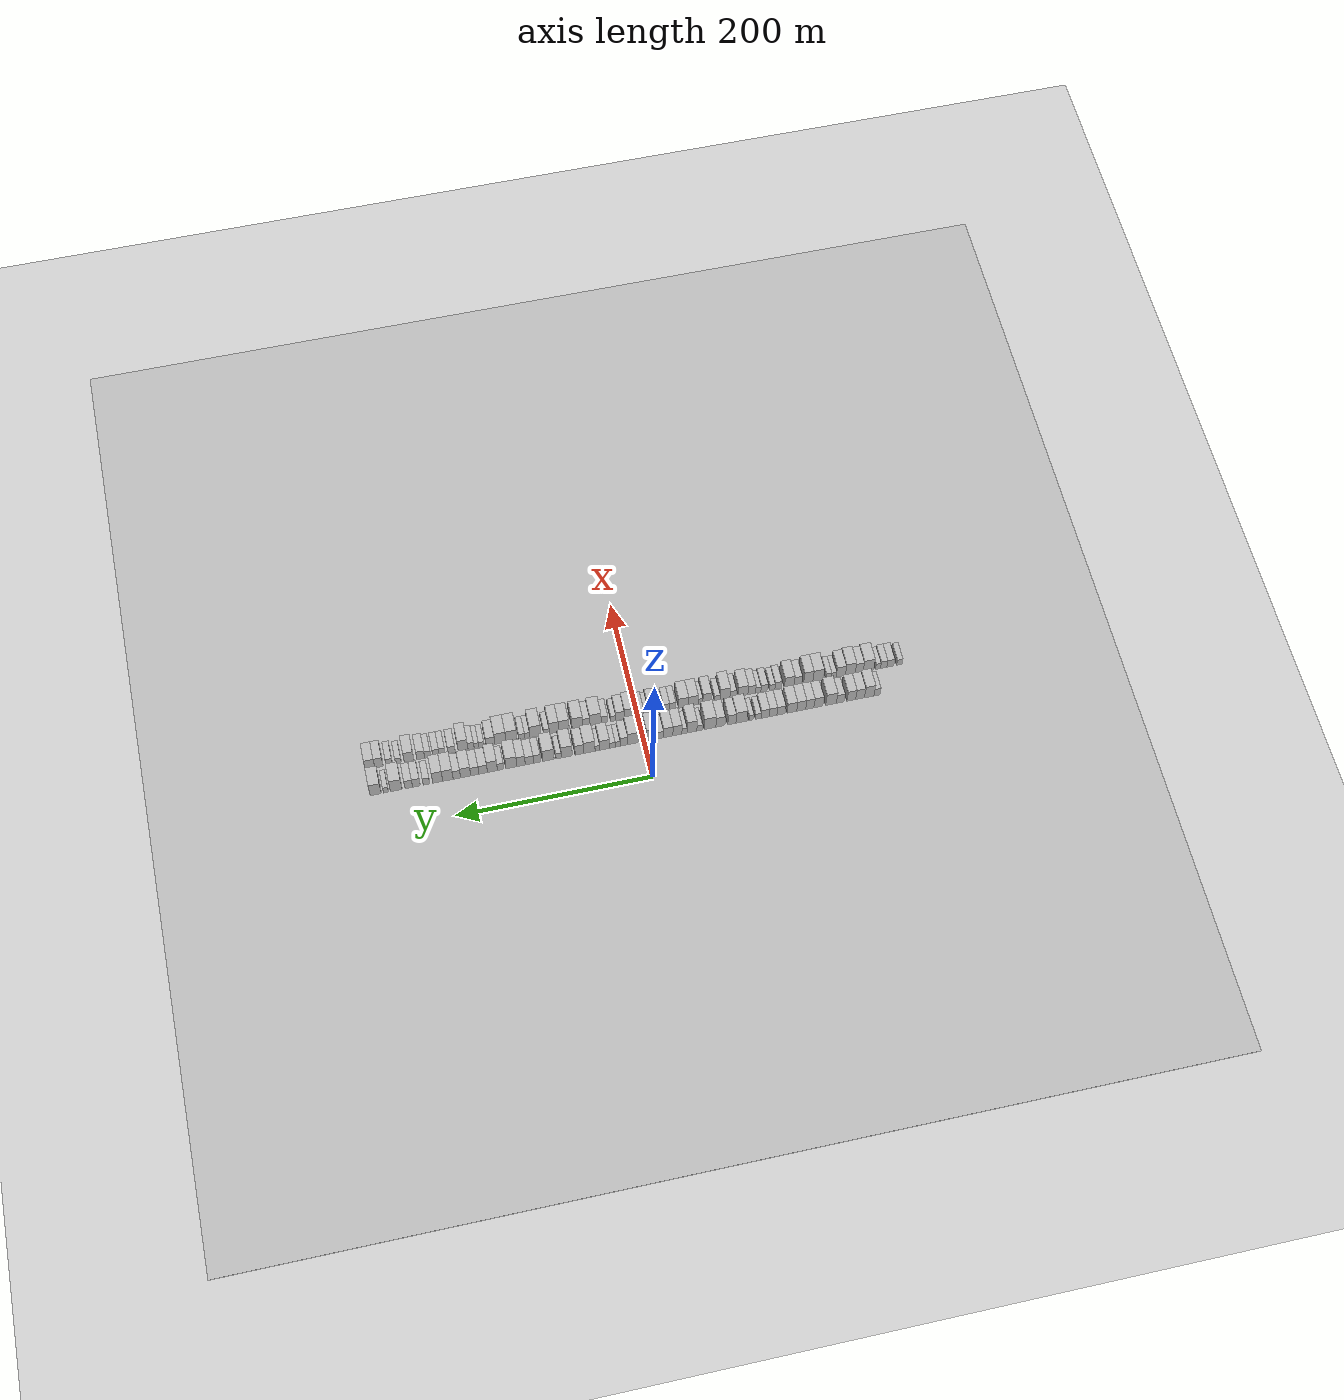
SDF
<?xml version="1.0" encoding="utf-8"?>

<sdf version="1.6">

   <world name="default">

      <gui fullscreen="0">

         <camera name="user_camera">

            <pose>-15 0 4.57585 0 0 0</pose>

            <view_controller>orbit</view_controller>

         </camera>

      </gui>

      <scene>

         <sky>

           <clouds>

             <speed>12</speed>

           </clouds>

         </sky>

         <ambient>0.4 0.4 0.4 1</ambient>

         <background>0.7 0.7 0.7 1</background>

         <shadows>1</shadows>

      </scene>

      <gravity>0 0 -9.8066</gravity>

      <magnetic_field>6e-06 2.3e-05 -4.2e-05</magnetic_field>

      <physics default="0" name="default_physics" type="ode">

         <ode>

            <solver>

               <type>quick</type>

               <iters>10</iters>

               <sor>1.0</sor>

               <use_dynamic_moi_rescaling>0</use_dynamic_moi_rescaling>

            </solver>

            <constraints>

               <cfm>0</cfm>

               <erp>0.2</erp>

               <contact_max_correcting_vel>100</contact_max_correcting_vel>

               <contact_surface_layer>0.001</contact_surface_layer>

            </constraints>

         </ode>

         <max_step_size>0.004</max_step_size>

         <real_time_factor>1</real_time_factor>

         <real_time_update_rate>250</real_time_update_rate>

      </physics>

      <light name="sun" type="directional">

         <cast_shadows>1</cast_shadows>

         <pose>0 0 10 0 0 0</pose>

         <diffuse>0.8 0.8 0.8 1</diffuse>

         <specular>0.2 0.2 0.2 1</specular>

         <attenuation>

            <range>1000</range>

            <constant>0.9</constant>

            <linear>0.01</linear>

            <quadratic>0.001</quadratic>

         </attenuation>

         <direction>-0.5 0.1 -0.9</direction>

      </light>

      <include>

         <name>ground_plane_1</name>

         <uri>model://HANNAS_ground_plane</uri>

         <pose>0 0 0  0 0 0</pose>

      </include>

      <include>

         <name>ground_plane_2</name>

         <uri>model://HANNAS_ground_plane</uri>

         <pose>100 0 0  0 0 0</pose>

      </include>

      <model name="building_1">

         <static>1</static>

         <pose frame="">50.0000 -243.4653 0 0.000000 0.000000 0.000000</pose>

         <link name="link">

            <pose frame="">0 0 7.50 0 0 0</pose>

            <collision name="collision">

               <geometry>

                  <box>

                     <size>20.0000 6.3565 15.0000</size>

                  </box>

               </geometry>

               <max_contacts>10</max_contacts>

               <surface>

                  <contact>

                     <ode/>

                  </contact>

                  <bounce/>

                  <friction>

                     <torsional>

                        <ode/>

                     </torsional>

                     <ode/>

                  </friction>

               </surface>

            </collision>

            <visual name="visual">

               <cast_shadows>0</cast_shadows>

               <geometry>

                  <box>

                     <size>20.0000 6.3565 15.0000</size>

                  </box>

               </geometry>

               <material>

                  <script>

                     <uri>model://HANNAS_wall/materials/scripts</uri>

                     <uri>model://HANNAS_wall/materials/textures</uri>

                     <name>vrc/HANNAS_wall</name>

                  </script>

               </material>

            </visual>

            <self_collide>0</self_collide>

            <enable_wind>0</enable_wind>

            <kinematic>0</kinematic>

         </link>

      </model>

      <model name="building_2">

         <static>1</static>

         <pose frame="">50.0000 -235.2615 0 0.000000 0.000000 0.000000</pose>

         <link name="link">

            <pose frame="">0 0 12.00 0 0 0</pose>

            <collision name="collision">

               <geometry>

                  <box>

                     <size>20.0000 10.0511 24.0000</size>

                  </box>

               </geometry>

               <max_contacts>10</max_contacts>

               <surface>

                  <contact>

                     <ode/>

                  </contact>

                  <bounce/>

                  <friction>

                     <torsional>

                        <ode/>

                     </torsional>

                     <ode/>

                  </friction>

               </surface>

            </collision>

            <visual name="visual">

               <cast_shadows>0</cast_shadows>

               <geometry>

                  <box>

                     <size>20.0000 10.0511 24.0000</size>

                  </box>

               </geometry>

               <material>

                  <script>

                     <uri>model://HANNAS_wall/materials/scripts</uri>

                     <uri>model://HANNAS_wall/materials/textures</uri>

                     <name>vrc/HANNAS_wall</name>

                  </script>

               </material>

            </visual>

            <self_collide>0</self_collide>

            <enable_wind>0</enable_wind>

            <kinematic>0</kinematic>

         </link>

      </model>

      <model name="building_3">

         <static>1</static>

         <pose frame="">50.0000 -225.6346 0 0.000000 0.000000 0.000000</pose>

         <link name="link">

            <pose frame="">0 0 10.50 0 0 0</pose>

            <collision name="collision">

               <geometry>

                  <box>

                     <size>20.0000 9.2027 21.0000</size>

                  </box>

               </geometry>

               <max_contacts>10</max_contacts>

               <surface>

                  <contact>

                     <ode/>

                  </contact>

                  <bounce/>

                  <friction>

                     <torsional>

                        <ode/>

                     </torsional>

                     <ode/>

                  </friction>

               </surface>

            </collision>

            <visual name="visual">

               <cast_shadows>0</cast_shadows>

               <geometry>

                  <box>

                     <size>20.0000 9.2027 21.0000</size>

                  </box>

               </geometry>

               <material>

                  <script>

                     <uri>model://HANNAS_wall/materials/scripts</uri>

                     <uri>model://HANNAS_wall/materials/textures</uri>

                     <name>vrc/HANNAS_wall</name>

                  </script>

               </material>

            </visual>

            <self_collide>0</self_collide>

            <enable_wind>0</enable_wind>

            <kinematic>0</kinematic>

         </link>

      </model>

      <model name="building_4">

         <static>1</static>

         <pose frame="">50.0000 -216.3543 0 0.000000 0.000000 0.000000</pose>

         <link name="link">

            <pose frame="">0 0 10.50 0 0 0</pose>

            <collision name="collision">

               <geometry>

                  <box>

                     <size>20.0000 9.3578 21.0000</size>

                  </box>

               </geometry>

               <max_contacts>10</max_contacts>

               <surface>

                  <contact>

                     <ode/>

                  </contact>

                  <bounce/>

                  <friction>

                     <torsional>

                        <ode/>

                     </torsional>

                     <ode/>

                  </friction>

               </surface>

            </collision>

            <visual name="visual">

               <cast_shadows>0</cast_shadows>

               <geometry>

                  <box>

                     <size>20.0000 9.3578 21.0000</size>

                  </box>

               </geometry>

               <material>

                  <script>

                     <uri>model://HANNAS_wall/materials/scripts</uri>

                     <uri>model://HANNAS_wall/materials/textures</uri>

                     <name>vrc/HANNAS_wall</name>

                  </script>

               </material>

            </visual>

            <self_collide>0</self_collide>

            <enable_wind>0</enable_wind>

            <kinematic>0</kinematic>

         </link>

      </model>

      <model name="building_5">

         <static>1</static>

         <pose frame="">50.0000 -204.6761 0 0.000000 0.000000 0.000000</pose>

         <link name="link">

            <pose frame="">0 0 9.00 0 0 0</pose>

            <collision name="collision">

               <geometry>

                  <box>

                     <size>20.0000 7.9984 18.0000</size>

                  </box>

               </geometry>

               <max_contacts>10</max_contacts>

               <surface>

                  <contact>

                     <ode/>

                  </contact>

                  <bounce/>

                  <friction>

                     <torsional>

                        <ode/>

                     </torsional>

                     <ode/>

                  </friction>

               </surface>

            </collision>

            <visual name="visual">

               <cast_shadows>0</cast_shadows>

               <geometry>

                  <box>

                     <size>20.0000 7.9984 18.0000</size>

                  </box>

               </geometry>

               <material>

                  <script>

                     <uri>model://HANNAS_wall/materials/scripts</uri>

                     <uri>model://HANNAS_wall/materials/textures</uri>

                     <name>vrc/HANNAS_wall</name>

                  </script>

               </material>

            </visual>

            <self_collide>0</self_collide>

            <enable_wind>0</enable_wind>

            <kinematic>0</kinematic>

         </link>

      </model>

      <model name="building_6">

         <static>1</static>

         <pose frame="">50.0000 -195.0604 0 0.000000 0.000000 0.000000</pose>

         <link name="link">

            <pose frame="">0 0 12.00 0 0 0</pose>

            <collision name="collision">

               <geometry>

                  <box>

                     <size>20.0000 11.2330 24.0000</size>

                  </box>

               </geometry>

               <max_contacts>10</max_contacts>

               <surface>

                  <contact>

                     <ode/>

                  </contact>

                  <bounce/>

                  <friction>

                     <torsional>

                        <ode/>

                     </torsional>

                     <ode/>

                  </friction>

               </surface>

            </collision>

            <visual name="visual">

               <cast_shadows>0</cast_shadows>

               <geometry>

                  <box>

                     <size>20.0000 11.2330 24.0000</size>

                  </box>

               </geometry>

               <material>

                  <script>

                     <uri>model://HANNAS_wall/materials/scripts</uri>

                     <uri>model://HANNAS_wall/materials/textures</uri>

                     <name>vrc/HANNAS_wall</name>

                  </script>

               </material>

            </visual>

            <self_collide>0</self_collide>

            <enable_wind>0</enable_wind>

            <kinematic>0</kinematic>

         </link>

      </model>

      <model name="building_7">

         <static>1</static>

         <pose frame="">50.0000 -181.7462 0 0.000000 0.000000 0.000000</pose>

         <link name="link">

            <pose frame="">0 0 10.50 0 0 0</pose>

            <collision name="collision">

               <geometry>

                  <box>

                     <size>20.0000 9.3955 21.0000</size>

                  </box>

               </geometry>

               <max_contacts>10</max_contacts>

               <surface>

                  <contact>

                     <ode/>

                  </contact>

                  <bounce/>

                  <friction>

                     <torsional>

                        <ode/>

                     </torsional>

                     <ode/>

                  </friction>

               </surface>

            </collision>

            <visual name="visual">

               <cast_shadows>0</cast_shadows>

               <geometry>

                  <box>

                     <size>20.0000 9.3955 21.0000</size>

                  </box>

               </geometry>

               <material>

                  <script>

                     <uri>model://HANNAS_wall/materials/scripts</uri>

                     <uri>model://HANNAS_wall/materials/textures</uri>

                     <name>vrc/HANNAS_wall</name>

                  </script>

               </material>

            </visual>

            <self_collide>0</self_collide>

            <enable_wind>0</enable_wind>

            <kinematic>0</kinematic>

         </link>

      </model>

      <model name="building_8">

         <static>1</static>

         <pose frame="">50.0000 -172.7809 0 0.000000 0.000000 0.000000</pose>

         <link name="link">

            <pose frame="">0 0 10.50 0 0 0</pose>

            <collision name="collision">

               <geometry>

                  <box>

                     <size>20.0000 8.5352 21.0000</size>

                  </box>

               </geometry>

               <max_contacts>10</max_contacts>

               <surface>

                  <contact>

                     <ode/>

                  </contact>

                  <bounce/>

                  <friction>

                     <torsional>

                        <ode/>

                     </torsional>

                     <ode/>

                  </friction>

               </surface>

            </collision>

            <visual name="visual">

               <cast_shadows>0</cast_shadows>

               <geometry>

                  <box>

                     <size>20.0000 8.5352 21.0000</size>

                  </box>

               </geometry>

               <material>

                  <script>

                     <uri>model://HANNAS_wall/materials/scripts</uri>

                     <uri>model://HANNAS_wall/materials/textures</uri>

                     <name>vrc/HANNAS_wall</name>

                  </script>

               </material>

            </visual>

            <self_collide>0</self_collide>

            <enable_wind>0</enable_wind>

            <kinematic>0</kinematic>

         </link>

      </model>

      <model name="building_9">

         <static>1</static>

         <pose frame="">50.0000 -163.7845 0 0.000000 0.000000 0.000000</pose>

         <link name="link">

            <pose frame="">0 0 10.50 0 0 0</pose>

            <collision name="collision">

               <geometry>

                  <box>

                     <size>20.0000 9.4576 21.0000</size>

                  </box>

               </geometry>

               <max_contacts>10</max_contacts>

               <surface>

                  <contact>

                     <ode/>

                  </contact>

                  <bounce/>

                  <friction>

                     <torsional>

                        <ode/>

                     </torsional>

                     <ode/>

                  </friction>

               </surface>

            </collision>

            <visual name="visual">

               <cast_shadows>0</cast_shadows>

               <geometry>

                  <box>

                     <size>20.0000 9.4576 21.0000</size>

                  </box>

               </geometry>

               <material>

                  <script>

                     <uri>model://HANNAS_wall/materials/scripts</uri>

                     <uri>model://HANNAS_wall/materials/textures</uri>

                     <name>vrc/HANNAS_wall</name>

                  </script>

               </material>

            </visual>

            <self_collide>0</self_collide>

            <enable_wind>0</enable_wind>

            <kinematic>0</kinematic>

         </link>

      </model>

      <model name="building_10">

         <static>1</static>

         <pose frame="">50.0000 -154.0091 0 0.000000 0.000000 0.000000</pose>

         <link name="link">

            <pose frame="">0 0 10.50 0 0 0</pose>

            <collision name="collision">

               <geometry>

                  <box>

                     <size>20.0000 10.0933 21.0000</size>

                  </box>

               </geometry>

               <max_contacts>10</max_contacts>

               <surface>

                  <contact>

                     <ode/>

                  </contact>

                  <bounce/>

                  <friction>

                     <torsional>

                        <ode/>

                     </torsional>

                     <ode/>

                  </friction>

               </surface>

            </collision>

            <visual name="visual">

               <cast_shadows>0</cast_shadows>

               <geometry>

                  <box>

                     <size>20.0000 10.0933 21.0000</size>

                  </box>

               </geometry>

               <material>

                  <script>

                     <uri>model://HANNAS_wall/materials/scripts</uri>

                     <uri>model://HANNAS_wall/materials/textures</uri>

                     <name>vrc/HANNAS_wall</name>

                  </script>

               </material>

            </visual>

            <self_collide>0</self_collide>

            <enable_wind>0</enable_wind>

            <kinematic>0</kinematic>

         </link>

      </model>

      <model name="building_11">

         <static>1</static>

         <pose frame="">50.0000 -142.6067 0 0.000000 0.000000 0.000000</pose>

         <link name="link">

            <pose frame="">0 0 9.00 0 0 0</pose>

            <collision name="collision">

               <geometry>

                  <box>

                     <size>20.0000 8.7116 18.0000</size>

                  </box>

               </geometry>

               <max_contacts>10</max_contacts>

               <surface>

                  <contact>

                     <ode/>

                  </contact>

                  <bounce/>

                  <friction>

                     <torsional>

                        <ode/>

                     </torsional>

                     <ode/>

                  </friction>

               </surface>

            </collision>

            <visual name="visual">

               <cast_shadows>0</cast_shadows>

               <geometry>

                  <box>

                     <size>20.0000 8.7116 18.0000</size>

                  </box>

               </geometry>

               <material>

                  <script>

                     <uri>model://HANNAS_wall/materials/scripts</uri>

                     <uri>model://HANNAS_wall/materials/textures</uri>

                     <name>vrc/HANNAS_wall</name>

                  </script>

               </material>

            </visual>

            <self_collide>0</self_collide>

            <enable_wind>0</enable_wind>

            <kinematic>0</kinematic>

         </link>

      </model>

      <model name="building_12">

         <static>1</static>

         <pose frame="">50.0000 -134.2623 0 0.000000 0.000000 0.000000</pose>

         <link name="link">

            <pose frame="">0 0 9.00 0 0 0</pose>

            <collision name="collision">

               <geometry>

                  <box>

                     <size>20.0000 7.9771 18.0000</size>

                  </box>

               </geometry>

               <max_contacts>10</max_contacts>

               <surface>

                  <contact>

                     <ode/>

                  </contact>

                  <bounce/>

                  <friction>

                     <torsional>

                        <ode/>

                     </torsional>

                     <ode/>

                  </friction>

               </surface>

            </collision>

            <visual name="visual">

               <cast_shadows>0</cast_shadows>

               <geometry>

                  <box>

                     <size>20.0000 7.9771 18.0000</size>

                  </box>

               </geometry>

               <material>

                  <script>

                     <uri>model://HANNAS_wall/materials/scripts</uri>

                     <uri>model://HANNAS_wall/materials/textures</uri>

                     <name>vrc/HANNAS_wall</name>

                  </script>

               </material>

            </visual>

            <self_collide>0</self_collide>

            <enable_wind>0</enable_wind>

            <kinematic>0</kinematic>

         </link>

      </model>

      <model name="building_13">

         <static>1</static>

         <pose frame="">50.0000 -125.9835 0 0.000000 0.000000 0.000000</pose>

         <link name="link">

            <pose frame="">0 0 9.00 0 0 0</pose>

            <collision name="collision">

               <geometry>

                  <box>

                     <size>20.0000 8.5806 18.0000</size>

                  </box>

               </geometry>

               <max_contacts>10</max_contacts>

               <surface>

                  <contact>

                     <ode/>

                  </contact>

                  <bounce/>

                  <friction>

                     <torsional>

                        <ode/>

                     </torsional>

                     <ode/>

                  </friction>

               </surface>

            </collision>

            <visual name="visual">

               <cast_shadows>0</cast_shadows>

               <geometry>

                  <box>

                     <size>20.0000 8.5806 18.0000</size>

                  </box>

               </geometry>

               <material>

                  <script>

                     <uri>model://HANNAS_wall/materials/scripts</uri>

                     <uri>model://HANNAS_wall/materials/textures</uri>

                     <name>vrc/HANNAS_wall</name>

                  </script>

               </material>

            </visual>

            <self_collide>0</self_collide>

            <enable_wind>0</enable_wind>

            <kinematic>0</kinematic>

         </link>

      </model>

      <model name="building_14">

         <static>1</static>

         <pose frame="">50.0000 -118.8375 0 0.000000 0.000000 0.000000</pose>

         <link name="link">

            <pose frame="">0 0 6.00 0 0 0</pose>

            <collision name="collision">

               <geometry>

                  <box>

                     <size>20.0000 5.7114 12.0000</size>

                  </box>

               </geometry>

               <max_contacts>10</max_contacts>

               <surface>

                  <contact>

                     <ode/>

                  </contact>

                  <bounce/>

                  <friction>

                     <torsional>

                        <ode/>

                     </torsional>

                     <ode/>

                  </friction>

               </surface>

            </collision>

            <visual name="visual">

               <cast_shadows>0</cast_shadows>

               <geometry>

                  <box>

                     <size>20.0000 5.7114 12.0000</size>

                  </box>

               </geometry>

               <material>

                  <script>

                     <uri>model://HANNAS_wall/materials/scripts</uri>

                     <uri>model://HANNAS_wall/materials/textures</uri>

                     <name>vrc/HANNAS_wall</name>

                  </script>

               </material>

            </visual>

            <self_collide>0</self_collide>

            <enable_wind>0</enable_wind>

            <kinematic>0</kinematic>

         </link>

      </model>

      <model name="building_15">

         <static>1</static>

         <pose frame="">50.0000 -111.5586 0 0.000000 0.000000 0.000000</pose>

         <link name="link">

            <pose frame="">0 0 6.00 0 0 0</pose>

            <collision name="collision">

               <geometry>

                  <box>

                     <size>20.0000 4.8464 12.0000</size>

                  </box>

               </geometry>

               <max_contacts>10</max_contacts>

               <surface>

                  <contact>

                     <ode/>

                  </contact>

                  <bounce/>

                  <friction>

                     <torsional>

                        <ode/>

                     </torsional>

                     <ode/>

                  </friction>

               </surface>

            </collision>

            <visual name="visual">

               <cast_shadows>0</cast_shadows>

               <geometry>

                  <box>

                     <size>20.0000 4.8464 12.0000</size>

                  </box>

               </geometry>

               <material>

                  <script>

                     <uri>model://HANNAS_wall/materials/scripts</uri>

                     <uri>model://HANNAS_wall/materials/textures</uri>

                     <name>vrc/HANNAS_wall</name>

                  </script>

               </material>

            </visual>

            <self_collide>0</self_collide>

            <enable_wind>0</enable_wind>

            <kinematic>0</kinematic>

         </link>

      </model>

      <model name="building_16">

         <static>1</static>

         <pose frame="">50.0000 -101.2901 0 0.000000 0.000000 0.000000</pose>

         <link name="link">

            <pose frame="">0 0 12.00 0 0 0</pose>

            <collision name="collision">

               <geometry>

                  <box>

                     <size>20.0000 11.6907 24.0000</size>

                  </box>

               </geometry>

               <max_contacts>10</max_contacts>

               <surface>

                  <contact>

                     <ode/>

                  </contact>

                  <bounce/>

                  <friction>

                     <torsional>

                        <ode/>

                     </torsional>

                     <ode/>

                  </friction>

               </surface>

            </collision>

            <visual name="visual">

               <cast_shadows>0</cast_shadows>

               <geometry>

                  <box>

                     <size>20.0000 11.6907 24.0000</size>

                  </box>

               </geometry>

               <material>

                  <script>

                     <uri>model://HANNAS_wall/materials/scripts</uri>

                     <uri>model://HANNAS_wall/materials/textures</uri>

                     <name>vrc/HANNAS_wall</name>

                  </script>

               </material>

            </visual>

            <self_collide>0</self_collide>

            <enable_wind>0</enable_wind>

            <kinematic>0</kinematic>

         </link>

      </model>

      <model name="building_17">

         <static>1</static>

         <pose frame="">50.0000 -91.2035 0 0.000000 0.000000 0.000000</pose>

         <link name="link">

            <pose frame="">0 0 10.50 0 0 0</pose>

            <collision name="collision">

               <geometry>

                  <box>

                     <size>20.0000 8.4825 21.0000</size>

                  </box>

               </geometry>

               <max_contacts>10</max_contacts>

               <surface>

                  <contact>

                     <ode/>

                  </contact>

                  <bounce/>

                  <friction>

                     <torsional>

                        <ode/>

                     </torsional>

                     <ode/>

                  </friction>

               </surface>

            </collision>

            <visual name="visual">

               <cast_shadows>0</cast_shadows>

               <geometry>

                  <box>

                     <size>20.0000 8.4825 21.0000</size>

                  </box>

               </geometry>

               <material>

                  <script>

                     <uri>model://HANNAS_wall/materials/scripts</uri>

                     <uri>model://HANNAS_wall/materials/textures</uri>

                     <name>vrc/HANNAS_wall</name>

                  </script>

               </material>

            </visual>

            <self_collide>0</self_collide>

            <enable_wind>0</enable_wind>

            <kinematic>0</kinematic>

         </link>

      </model>

      <model name="building_18">

         <static>1</static>

         <pose frame="">50.0000 -79.2576 0 0.000000 0.000000 0.000000</pose>

         <link name="link">

            <pose frame="">0 0 10.50 0 0 0</pose>

            <collision name="collision">

               <geometry>

                  <box>

                     <size>20.0000 9.4094 21.0000</size>

                  </box>

               </geometry>

               <max_contacts>10</max_contacts>

               <surface>

                  <contact>

                     <ode/>

                  </contact>

                  <bounce/>

                  <friction>

                     <torsional>

                        <ode/>

                     </torsional>

                     <ode/>

                  </friction>

               </surface>

            </collision>

            <visual name="visual">

               <cast_shadows>0</cast_shadows>

               <geometry>

                  <box>

                     <size>20.0000 9.4094 21.0000</size>

                  </box>

               </geometry>

               <material>

                  <script>

                     <uri>model://HANNAS_wall/materials/scripts</uri>

                     <uri>model://HANNAS_wall/materials/textures</uri>

                     <name>vrc/HANNAS_wall</name>

                  </script>

               </material>

            </visual>

            <self_collide>0</self_collide>

            <enable_wind>0</enable_wind>

            <kinematic>0</kinematic>

         </link>

      </model>

      <model name="building_19">

         <static>1</static>

         <pose frame="">50.0000 -68.5814 0 0.000000 0.000000 0.000000</pose>

         <link name="link">

            <pose frame="">0 0 12.00 0 0 0</pose>

            <collision name="collision">

               <geometry>

                  <box>

                     <size>20.0000 11.9430 24.0000</size>

                  </box>

               </geometry>

               <max_contacts>10</max_contacts>

               <surface>

                  <contact>

                     <ode/>

                  </contact>

                  <bounce/>

                  <friction>

                     <torsional>

                        <ode/>

                     </torsional>

                     <ode/>

                  </friction>

               </surface>

            </collision>

            <visual name="visual">

               <cast_shadows>0</cast_shadows>

               <geometry>

                  <box>

                     <size>20.0000 11.9430 24.0000</size>

                  </box>

               </geometry>

               <material>

                  <script>

                     <uri>model://HANNAS_wall/materials/scripts</uri>

                     <uri>model://HANNAS_wall/materials/textures</uri>

                     <name>vrc/HANNAS_wall</name>

                  </script>

               </material>

            </visual>

            <self_collide>0</self_collide>

            <enable_wind>0</enable_wind>

            <kinematic>0</kinematic>

         </link>

      </model>

      <model name="building_20">

         <static>1</static>

         <pose frame="">50.0000 -57.6788 0 0.000000 0.000000 0.000000</pose>

         <link name="link">

            <pose frame="">0 0 6.00 0 0 0</pose>

            <collision name="collision">

               <geometry>

                  <box>

                     <size>20.0000 5.8621 12.0000</size>

                  </box>

               </geometry>

               <max_contacts>10</max_contacts>

               <surface>

                  <contact>

                     <ode/>

                  </contact>

                  <bounce/>

                  <friction>

                     <torsional>

                        <ode/>

                     </torsional>

                     <ode/>

                  </friction>

               </surface>

            </collision>

            <visual name="visual">

               <cast_shadows>0</cast_shadows>

               <geometry>

                  <box>

                     <size>20.0000 5.8621 12.0000</size>

                  </box>

               </geometry>

               <material>

                  <script>

                     <uri>model://HANNAS_wall/materials/scripts</uri>

                     <uri>model://HANNAS_wall/materials/textures</uri>

                     <name>vrc/HANNAS_wall</name>

                  </script>

               </material>

            </visual>

            <self_collide>0</self_collide>

            <enable_wind>0</enable_wind>

            <kinematic>0</kinematic>

         </link>

      </model>

      <model name="building_21">

         <static>1</static>

         <pose frame="">50.0000 -49.6550 0 0.000000 0.000000 0.000000</pose>

         <link name="link">

            <pose frame="">0 0 12.00 0 0 0</pose>

            <collision name="collision">

               <geometry>

                  <box>

                     <size>20.0000 10.1855 24.0000</size>

                  </box>

               </geometry>

               <max_contacts>10</max_contacts>

               <surface>

                  <contact>

                     <ode/>

                  </contact>

                  <bounce/>

                  <friction>

                     <torsional>

                        <ode/>

                     </torsional>

                     <ode/>

                  </friction>

               </surface>

            </collision>

            <visual name="visual">

               <cast_shadows>0</cast_shadows>

               <geometry>

                  <box>

                     <size>20.0000 10.1855 24.0000</size>

                  </box>

               </geometry>

               <material>

                  <script>

                     <uri>model://HANNAS_wall/materials/scripts</uri>

                     <uri>model://HANNAS_wall/materials/textures</uri>

                     <name>vrc/HANNAS_wall</name>

                  </script>

               </material>

            </visual>

            <self_collide>0</self_collide>

            <enable_wind>0</enable_wind>

            <kinematic>0</kinematic>

         </link>

      </model>

      <model name="building_22">

         <static>1</static>

         <pose frame="">50.0000 -41.8930 0 0.000000 0.000000 0.000000</pose>

         <link name="link">

            <pose frame="">0 0 6.00 0 0 0</pose>

            <collision name="collision">

               <geometry>

                  <box>

                     <size>20.0000 5.3385 12.0000</size>

                  </box>

               </geometry>

               <max_contacts>10</max_contacts>

               <surface>

                  <contact>

                     <ode/>

                  </contact>

                  <bounce/>

                  <friction>

                     <torsional>

                        <ode/>

                     </torsional>

                     <ode/>

                  </friction>

               </surface>

            </collision>

            <visual name="visual">

               <cast_shadows>0</cast_shadows>

               <geometry>

                  <box>

                     <size>20.0000 5.3385 12.0000</size>

                  </box>

               </geometry>

               <material>

                  <script>

                     <uri>model://HANNAS_wall/materials/scripts</uri>

                     <uri>model://HANNAS_wall/materials/textures</uri>

                     <name>vrc/HANNAS_wall</name>

                  </script>

               </material>

            </visual>

            <self_collide>0</self_collide>

            <enable_wind>0</enable_wind>

            <kinematic>0</kinematic>

         </link>

      </model>

      <model name="building_23">

         <static>1</static>

         <pose frame="">50.0000 -34.5507 0 0.000000 0.000000 0.000000</pose>

         <link name="link">

            <pose frame="">0 0 10.50 0 0 0</pose>

            <collision name="collision">

               <geometry>

                  <box>

                     <size>20.0000 9.3463 21.0000</size>

                  </box>

               </geometry>

               <max_contacts>10</max_contacts>

               <surface>

                  <contact>

                     <ode/>

                  </contact>

                  <bounce/>

                  <friction>

                     <torsional>

                        <ode/>

                     </torsional>

                     <ode/>

                  </friction>

               </surface>

            </collision>

            <visual name="visual">

               <cast_shadows>0</cast_shadows>

               <geometry>

                  <box>

                     <size>20.0000 9.3463 21.0000</size>

                  </box>

               </geometry>

               <material>

                  <script>

                     <uri>model://HANNAS_wall/materials/scripts</uri>

                     <uri>model://HANNAS_wall/materials/textures</uri>

                     <name>vrc/HANNAS_wall</name>

                  </script>

               </material>

            </visual>

            <self_collide>0</self_collide>

            <enable_wind>0</enable_wind>

            <kinematic>0</kinematic>

         </link>

      </model>

      <model name="building_24">

         <static>1</static>

         <pose frame="">50.0000 -25.0386 0 0.000000 0.000000 0.000000</pose>

         <link name="link">

            <pose frame="">0 0 10.50 0 0 0</pose>

            <collision name="collision">

               <geometry>

                  <box>

                     <size>20.0000 9.6778 21.0000</size>

                  </box>

               </geometry>

               <max_contacts>10</max_contacts>

               <surface>

                  <contact>

                     <ode/>

                  </contact>

                  <bounce/>

                  <friction>

                     <torsional>

                        <ode/>

                     </torsional>

                     <ode/>

                  </friction>

               </surface>

            </collision>

            <visual name="visual">

               <cast_shadows>0</cast_shadows>

               <geometry>

                  <box>

                     <size>20.0000 9.6778 21.0000</size>

                  </box>

               </geometry>

               <material>

                  <script>

                     <uri>model://HANNAS_wall/materials/scripts</uri>

                     <uri>model://HANNAS_wall/materials/textures</uri>

                     <name>vrc/HANNAS_wall</name>

                  </script>

               </material>

            </visual>

            <self_collide>0</self_collide>

            <enable_wind>0</enable_wind>

            <kinematic>0</kinematic>

         </link>

      </model>

      <model name="building_25">

         <static>1</static>

         <pose frame="">50.0000 -17.0260 0 0.000000 0.000000 0.000000</pose>

         <link name="link">

            <pose frame="">0 0 7.50 0 0 0</pose>

            <collision name="collision">

               <geometry>

                  <box>

                     <size>20.0000 6.3474 15.0000</size>

                  </box>

               </geometry>

               <max_contacts>10</max_contacts>

               <surface>

                  <contact>

                     <ode/>

                  </contact>

                  <bounce/>

                  <friction>

                     <torsional>

                        <ode/>

                     </torsional>

                     <ode/>

                  </friction>

               </surface>

            </collision>

            <visual name="visual">

               <cast_shadows>0</cast_shadows>

               <geometry>

                  <box>

                     <size>20.0000 6.3474 15.0000</size>

                  </box>

               </geometry>

               <material>

                  <script>

                     <uri>model://HANNAS_wall/materials/scripts</uri>

                     <uri>model://HANNAS_wall/materials/textures</uri>

                     <name>vrc/HANNAS_wall</name>

                  </script>

               </material>

            </visual>

            <self_collide>0</self_collide>

            <enable_wind>0</enable_wind>

            <kinematic>0</kinematic>

         </link>

      </model>

      <model name="building_26">

         <static>1</static>

         <pose frame="">50.0000 -8.1673 0 0.000000 0.000000 0.000000</pose>

         <link name="link">

            <pose frame="">0 0 12.00 0 0 0</pose>

            <collision name="collision">

               <geometry>

                  <box>

                     <size>20.0000 11.3700 24.0000</size>

                  </box>

               </geometry>

               <max_contacts>10</max_contacts>

               <surface>

                  <contact>

                     <ode/>

                  </contact>

                  <bounce/>

                  <friction>

                     <torsional>

                        <ode/>

                     </torsional>

                     <ode/>

                  </friction>

               </surface>

            </collision>

            <visual name="visual">

               <cast_shadows>0</cast_shadows>

               <geometry>

                  <box>

                     <size>20.0000 11.3700 24.0000</size>

                  </box>

               </geometry>

               <material>

                  <script>

                     <uri>model://HANNAS_wall/materials/scripts</uri>

                     <uri>model://HANNAS_wall/materials/textures</uri>

                     <name>vrc/HANNAS_wall</name>

                  </script>

               </material>

            </visual>

            <self_collide>0</self_collide>

            <enable_wind>0</enable_wind>

            <kinematic>0</kinematic>

         </link>

      </model>

      <model name="building_27">

         <static>1</static>

         <pose frame="">50.0000 0.0869 0 0.000000 0.000000 0.000000</pose>

         <link name="link">

            <pose frame="">0 0 6.00 0 0 0</pose>

            <collision name="collision">

               <geometry>

                  <box>

                     <size>20.0000 5.1384 12.0000</size>

                  </box>

               </geometry>

               <max_contacts>10</max_contacts>

               <surface>

                  <contact>

                     <ode/>

                  </contact>

                  <bounce/>

                  <friction>

                     <torsional>

                        <ode/>

                     </torsional>

                     <ode/>

                  </friction>

               </surface>

            </collision>

            <visual name="visual">

               <cast_shadows>0</cast_shadows>

               <geometry>

                  <box>

                     <size>20.0000 5.1384 12.0000</size>

                  </box>

               </geometry>

               <material>

                  <script>

                     <uri>model://HANNAS_wall/materials/scripts</uri>

                     <uri>model://HANNAS_wall/materials/textures</uri>

                     <name>vrc/HANNAS_wall</name>

                  </script>

               </material>

            </visual>

            <self_collide>0</self_collide>

            <enable_wind>0</enable_wind>

            <kinematic>0</kinematic>

         </link>

      </model>

      <model name="building_28">

         <static>1</static>

         <pose frame="">50.0000 11.1717 0 0.000000 0.000000 0.000000</pose>

         <link name="link">

            <pose frame="">0 0 12.00 0 0 0</pose>

            <collision name="collision">

               <geometry>

                  <box>

                     <size>20.0000 11.0312 24.0000</size>

                  </box>

               </geometry>

               <max_contacts>10</max_contacts>

               <surface>

                  <contact>

                     <ode/>

                  </contact>

                  <bounce/>

                  <friction>

                     <torsional>

                        <ode/>

                     </torsional>

                     <ode/>

                  </friction>

               </surface>

            </collision>

            <visual name="visual">

               <cast_shadows>0</cast_shadows>

               <geometry>

                  <box>

                     <size>20.0000 11.0312 24.0000</size>

                  </box>

               </geometry>

               <material>

                  <script>

                     <uri>model://HANNAS_wall/materials/scripts</uri>

                     <uri>model://HANNAS_wall/materials/textures</uri>

                     <name>vrc/HANNAS_wall</name>

                  </script>

               </material>

            </visual>

            <self_collide>0</self_collide>

            <enable_wind>0</enable_wind>

            <kinematic>0</kinematic>

         </link>

      </model>

      <model name="building_29">

         <static>1</static>

         <pose frame="">50.0000 20.5993 0 0.000000 0.000000 0.000000</pose>

         <link name="link">

            <pose frame="">0 0 9.00 0 0 0</pose>

            <collision name="collision">

               <geometry>

                  <box>

                     <size>20.0000 7.8240 18.0000</size>

                  </box>

               </geometry>

               <max_contacts>10</max_contacts>

               <surface>

                  <contact>

                     <ode/>

                  </contact>

                  <bounce/>

                  <friction>

                     <torsional>

                        <ode/>

                     </torsional>

                     <ode/>

                  </friction>

               </surface>

            </collision>

            <visual name="visual">

               <cast_shadows>0</cast_shadows>

               <geometry>

                  <box>

                     <size>20.0000 7.8240 18.0000</size>

                  </box>

               </geometry>

               <material>

                  <script>

                     <uri>model://HANNAS_wall/materials/scripts</uri>

                     <uri>model://HANNAS_wall/materials/textures</uri>

                     <name>vrc/HANNAS_wall</name>

                  </script>

               </material>

            </visual>

            <self_collide>0</self_collide>

            <enable_wind>0</enable_wind>

            <kinematic>0</kinematic>

         </link>

      </model>

      <model name="building_30">

         <static>1</static>

         <pose frame="">50.0000 27.1070 0 0.000000 0.000000 0.000000</pose>

         <link name="link">

            <pose frame="">0 0 6.00 0 0 0</pose>

            <collision name="collision">

               <geometry>

                  <box>

                     <size>20.0000 5.1913 12.0000</size>

                  </box>

               </geometry>

               <max_contacts>10</max_contacts>

               <surface>

                  <contact>

                     <ode/>

                  </contact>

                  <bounce/>

                  <friction>

                     <torsional>

                        <ode/>

                     </torsional>

                     <ode/>

                  </friction>

               </surface>

            </collision>

            <visual name="visual">

               <cast_shadows>0</cast_shadows>

               <geometry>

                  <box>

                     <size>20.0000 5.1913 12.0000</size>

                  </box>

               </geometry>

               <material>

                  <script>

                     <uri>model://HANNAS_wall/materials/scripts</uri>

                     <uri>model://HANNAS_wall/materials/textures</uri>

                     <name>vrc/HANNAS_wall</name>

                  </script>

               </material>

            </visual>

            <self_collide>0</self_collide>

            <enable_wind>0</enable_wind>

            <kinematic>0</kinematic>

         </link>

      </model>

      <model name="building_31">

         <static>1</static>

         <pose frame="">50.0000 32.6259 0 0.000000 0.000000 0.000000</pose>

         <link name="link">

            <pose frame="">0 0 6.00 0 0 0</pose>

            <collision name="collision">

               <geometry>

                  <box>

                     <size>20.0000 5.8464 12.0000</size>

                  </box>

               </geometry>

               <max_contacts>10</max_contacts>

               <surface>

                  <contact>

                     <ode/>

                  </contact>

                  <bounce/>

                  <friction>

                     <torsional>

                        <ode/>

                     </torsional>

                     <ode/>

                  </friction>

               </surface>

            </collision>

            <visual name="visual">

               <cast_shadows>0</cast_shadows>

               <geometry>

                  <box>

                     <size>20.0000 5.8464 12.0000</size>

                  </box>

               </geometry>

               <material>

                  <script>

                     <uri>model://HANNAS_wall/materials/scripts</uri>

                     <uri>model://HANNAS_wall/materials/textures</uri>

                     <name>vrc/HANNAS_wall</name>

                  </script>

               </material>

            </visual>

            <self_collide>0</self_collide>

            <enable_wind>0</enable_wind>

            <kinematic>0</kinematic>

         </link>

      </model>

      <model name="building_32">

         <static>1</static>

         <pose frame="">50.0000 40.5985 0 0.000000 0.000000 0.000000</pose>

         <link name="link">

            <pose frame="">0 0 10.50 0 0 0</pose>

            <collision name="collision">

               <geometry>

                  <box>

                     <size>20.0000 10.0989 21.0000</size>

                  </box>

               </geometry>

               <max_contacts>10</max_contacts>

               <surface>

                  <contact>

                     <ode/>

                  </contact>

                  <bounce/>

                  <friction>

                     <torsional>

                        <ode/>

                     </torsional>

                     <ode/>

                  </friction>

               </surface>

            </collision>

            <visual name="visual">

               <cast_shadows>0</cast_shadows>

               <geometry>

                  <box>

                     <size>20.0000 10.0989 21.0000</size>

                  </box>

               </geometry>

               <material>

                  <script>

                     <uri>model://HANNAS_wall/materials/scripts</uri>

                     <uri>model://HANNAS_wall/materials/textures</uri>

                     <name>vrc/HANNAS_wall</name>

                  </script>

               </material>

            </visual>

            <self_collide>0</self_collide>

            <enable_wind>0</enable_wind>

            <kinematic>0</kinematic>

         </link>

      </model>

      <model name="building_33">

         <static>1</static>

         <pose frame="">50.0000 48.1005 0 0.000000 0.000000 0.000000</pose>

         <link name="link">

            <pose frame="">0 0 6.00 0 0 0</pose>

            <collision name="collision">

               <geometry>

                  <box>

                     <size>20.0000 4.9049 12.0000</size>

                  </box>

               </geometry>

               <max_contacts>10</max_contacts>

               <surface>

                  <contact>

                     <ode/>

                  </contact>

                  <bounce/>

                  <friction>

                     <torsional>

                        <ode/>

                     </torsional>

                     <ode/>

                  </friction>

               </surface>

            </collision>

            <visual name="visual">

               <cast_shadows>0</cast_shadows>

               <geometry>

                  <box>

                     <size>20.0000 4.9049 12.0000</size>

                  </box>

               </geometry>

               <material>

                  <script>

                     <uri>model://HANNAS_wall/materials/scripts</uri>

                     <uri>model://HANNAS_wall/materials/textures</uri>

                     <name>vrc/HANNAS_wall</name>

                  </script>

               </material>

            </visual>

            <self_collide>0</self_collide>

            <enable_wind>0</enable_wind>

            <kinematic>0</kinematic>

         </link>

      </model>

      <model name="building_34">

         <static>1</static>

         <pose frame="">50.0000 56.3387 0 0.000000 0.000000 0.000000</pose>

         <link name="link">

            <pose frame="">0 0 12.00 0 0 0</pose>

            <collision name="collision">

               <geometry>

                  <box>

                     <size>20.0000 11.5715 24.0000</size>

                  </box>

               </geometry>

               <max_contacts>10</max_contacts>

               <surface>

                  <contact>

                     <ode/>

                  </contact>

                  <bounce/>

                  <friction>

                     <torsional>

                        <ode/>

                     </torsional>

                     <ode/>

                  </friction>

               </surface>

            </collision>

            <visual name="visual">

               <cast_shadows>0</cast_shadows>

               <geometry>

                  <box>

                     <size>20.0000 11.5715 24.0000</size>

                  </box>

               </geometry>

               <material>

                  <script>

                     <uri>model://HANNAS_wall/materials/scripts</uri>

                     <uri>model://HANNAS_wall/materials/textures</uri>

                     <name>vrc/HANNAS_wall</name>

                  </script>

               </material>

            </visual>

            <self_collide>0</self_collide>

            <enable_wind>0</enable_wind>

            <kinematic>0</kinematic>

         </link>

      </model>

      <model name="building_35">

         <static>1</static>

         <pose frame="">50.0000 66.5732 0 0.000000 0.000000 0.000000</pose>

         <link name="link">

            <pose frame="">0 0 10.50 0 0 0</pose>

            <collision name="collision">

               <geometry>

                  <box>

                     <size>20.0000 8.8975 21.0000</size>

                  </box>

               </geometry>

               <max_contacts>10</max_contacts>

               <surface>

                  <contact>

                     <ode/>

                  </contact>

                  <bounce/>

                  <friction>

                     <torsional>

                        <ode/>

                     </torsional>

                     <ode/>

                  </friction>

               </surface>

            </collision>

            <visual name="visual">

               <cast_shadows>0</cast_shadows>

               <geometry>

                  <box>

                     <size>20.0000 8.8975 21.0000</size>

                  </box>

               </geometry>

               <material>

                  <script>

                     <uri>model://HANNAS_wall/materials/scripts</uri>

                     <uri>model://HANNAS_wall/materials/textures</uri>

                     <name>vrc/HANNAS_wall</name>

                  </script>

               </material>

            </visual>

            <self_collide>0</self_collide>

            <enable_wind>0</enable_wind>

            <kinematic>0</kinematic>

         </link>

      </model>

      <model name="building_36">

         <static>1</static>

         <pose frame="">50.0000 79.5994 0 0.000000 0.000000 0.000000</pose>

         <link name="link">

            <pose frame="">0 0 12.00 0 0 0</pose>

            <collision name="collision">

               <geometry>

                  <box>

                     <size>20.0000 11.1550 24.0000</size>

                  </box>

               </geometry>

               <max_contacts>10</max_contacts>

               <surface>

                  <contact>

                     <ode/>

                  </contact>

                  <bounce/>

                  <friction>

                     <torsional>

                        <ode/>

                     </torsional>

                     <ode/>

                  </friction>

               </surface>

            </collision>

            <visual name="visual">

               <cast_shadows>0</cast_shadows>

               <geometry>

                  <box>

                     <size>20.0000 11.1550 24.0000</size>

                  </box>

               </geometry>

               <material>

                  <script>

                     <uri>model://HANNAS_wall/materials/scripts</uri>

                     <uri>model://HANNAS_wall/materials/textures</uri>

                     <name>vrc/HANNAS_wall</name>

                  </script>

               </material>

            </visual>

            <self_collide>0</self_collide>

            <enable_wind>0</enable_wind>

            <kinematic>0</kinematic>

         </link>

      </model>

      <model name="building_37">

         <static>1</static>

         <pose frame="">50.0000 87.9173 0 0.000000 0.000000 0.000000</pose>

         <link name="link">

            <pose frame="">0 0 6.00 0 0 0</pose>

            <collision name="collision">

               <geometry>

                  <box>

                     <size>20.0000 5.4807 12.0000</size>

                  </box>

               </geometry>

               <max_contacts>10</max_contacts>

               <surface>

                  <contact>

                     <ode/>

                  </contact>

                  <bounce/>

                  <friction>

                     <torsional>

                        <ode/>

                     </torsional>

                     <ode/>

                  </friction>

               </surface>

            </collision>

            <visual name="visual">

               <cast_shadows>0</cast_shadows>

               <geometry>

                  <box>

                     <size>20.0000 5.4807 12.0000</size>

                  </box>

               </geometry>

               <material>

                  <script>

                     <uri>model://HANNAS_wall/materials/scripts</uri>

                     <uri>model://HANNAS_wall/materials/textures</uri>

                     <name>vrc/HANNAS_wall</name>

                  </script>

               </material>

            </visual>

            <self_collide>0</self_collide>

            <enable_wind>0</enable_wind>

            <kinematic>0</kinematic>

         </link>

      </model>

      <model name="building_38">

         <static>1</static>

         <pose frame="">50.0000 98.5186 0 0.000000 0.000000 0.000000</pose>

         <link name="link">

            <pose frame="">0 0 12.00 0 0 0</pose>

            <collision name="collision">

               <geometry>

                  <box>

                     <size>20.0000 11.7219 24.0000</size>

                  </box>

               </geometry>

               <max_contacts>10</max_contacts>

               <surface>

                  <contact>

                     <ode/>

                  </contact>

                  <bounce/>

                  <friction>

                     <torsional>

                        <ode/>

                     </torsional>

                     <ode/>

                  </friction>

               </surface>

            </collision>

            <visual name="visual">

               <cast_shadows>0</cast_shadows>

               <geometry>

                  <box>

                     <size>20.0000 11.7219 24.0000</size>

                  </box>

               </geometry>

               <material>

                  <script>

                     <uri>model://HANNAS_wall/materials/scripts</uri>

                     <uri>model://HANNAS_wall/materials/textures</uri>

                     <name>vrc/HANNAS_wall</name>

                  </script>

               </material>

            </visual>

            <self_collide>0</self_collide>

            <enable_wind>0</enable_wind>

            <kinematic>0</kinematic>

         </link>

      </model>

      <model name="building_39">

         <static>1</static>

         <pose frame="">50.0000 109.9865 0 0.000000 0.000000 0.000000</pose>

         <link name="link">

            <pose frame="">0 0 9.00 0 0 0</pose>

            <collision name="collision">

               <geometry>

                  <box>

                     <size>20.0000 7.2139 18.0000</size>

                  </box>

               </geometry>

               <max_contacts>10</max_contacts>

               <surface>

                  <contact>

                     <ode/>

                  </contact>

                  <bounce/>

                  <friction>

                     <torsional>

                        <ode/>

                     </torsional>

                     <ode/>

                  </friction>

               </surface>

            </collision>

            <visual name="visual">

               <cast_shadows>0</cast_shadows>

               <geometry>

                  <box>

                     <size>20.0000 7.2139 18.0000</size>

                  </box>

               </geometry>

               <material>

                  <script>

                     <uri>model://HANNAS_wall/materials/scripts</uri>

                     <uri>model://HANNAS_wall/materials/textures</uri>

                     <name>vrc/HANNAS_wall</name>

                  </script>

               </material>

            </visual>

            <self_collide>0</self_collide>

            <enable_wind>0</enable_wind>

            <kinematic>0</kinematic>

         </link>

      </model>

      <model name="building_40">

         <static>1</static>

         <pose frame="">50.0000 117.9040 0 0.000000 0.000000 0.000000</pose>

         <link name="link">

            <pose frame="">0 0 9.00 0 0 0</pose>

            <collision name="collision">

               <geometry>

                  <box>

                     <size>20.0000 8.6211 18.0000</size>

                  </box>

               </geometry>

               <max_contacts>10</max_contacts>

               <surface>

                  <contact>

                     <ode/>

                  </contact>

                  <bounce/>

                  <friction>

                     <torsional>

                        <ode/>

                     </torsional>

                     <ode/>

                  </friction>

               </surface>

            </collision>

            <visual name="visual">

               <cast_shadows>0</cast_shadows>

               <geometry>

                  <box>

                     <size>20.0000 8.6211 18.0000</size>

                  </box>

               </geometry>

               <material>

                  <script>

                     <uri>model://HANNAS_wall/materials/scripts</uri>

                     <uri>model://HANNAS_wall/materials/textures</uri>

                     <name>vrc/HANNAS_wall</name>

                  </script>

               </material>

            </visual>

            <self_collide>0</self_collide>

            <enable_wind>0</enable_wind>

            <kinematic>0</kinematic>

         </link>

      </model>

      <model name="building_41">

         <static>1</static>

         <pose frame="">50.0000 126.5039 0 0.000000 0.000000 0.000000</pose>

         <link name="link">

            <pose frame="">0 0 10.50 0 0 0</pose>

            <collision name="collision">

               <geometry>

                  <box>

                     <size>20.0000 8.5786 21.0000</size>

                  </box>

               </geometry>

               <max_contacts>10</max_contacts>

               <surface>

                  <contact>

                     <ode/>

                  </contact>

                  <bounce/>

                  <friction>

                     <torsional>

                        <ode/>

                     </torsional>

                     <ode/>

                  </friction>

               </surface>

            </collision>

            <visual name="visual">

               <cast_shadows>0</cast_shadows>

               <geometry>

                  <box>

                     <size>20.0000 8.5786 21.0000</size>

                  </box>

               </geometry>

               <material>

                  <script>

                     <uri>model://HANNAS_wall/materials/scripts</uri>

                     <uri>model://HANNAS_wall/materials/textures</uri>

                     <name>vrc/HANNAS_wall</name>

                  </script>

               </material>

            </visual>

            <self_collide>0</self_collide>

            <enable_wind>0</enable_wind>

            <kinematic>0</kinematic>

         </link>

      </model>

      <model name="building_42">

         <static>1</static>

         <pose frame="">50.0000 136.4017 0 0.000000 0.000000 0.000000</pose>

         <link name="link">

            <pose frame="">0 0 12.00 0 0 0</pose>

            <collision name="collision">

               <geometry>

                  <box>

                     <size>20.0000 11.2170 24.0000</size>

                  </box>

               </geometry>

               <max_contacts>10</max_contacts>

               <surface>

                  <contact>

                     <ode/>

                  </contact>

                  <bounce/>

                  <friction>

                     <torsional>

                        <ode/>

                     </torsional>

                     <ode/>

                  </friction>

               </surface>

            </collision>

            <visual name="visual">

               <cast_shadows>0</cast_shadows>

               <geometry>

                  <box>

                     <size>20.0000 11.2170 24.0000</size>

                  </box>

               </geometry>

               <material>

                  <script>

                     <uri>model://HANNAS_wall/materials/scripts</uri>

                     <uri>model://HANNAS_wall/materials/textures</uri>

                     <name>vrc/HANNAS_wall</name>

                  </script>

               </material>

            </visual>

            <self_collide>0</self_collide>

            <enable_wind>0</enable_wind>

            <kinematic>0</kinematic>

         </link>

      </model>

      <model name="building_43">

         <static>1</static>

         <pose frame="">50.0000 147.2961 0 0.000000 0.000000 0.000000</pose>

         <link name="link">

            <pose frame="">0 0 7.50 0 0 0</pose>

            <collision name="collision">

               <geometry>

                  <box>

                     <size>20.0000 6.5718 15.0000</size>

                  </box>

               </geometry>

               <max_contacts>10</max_contacts>

               <surface>

                  <contact>

                     <ode/>

                  </contact>

                  <bounce/>

                  <friction>

                     <torsional>

                        <ode/>

                     </torsional>

                     <ode/>

                  </friction>

               </surface>

            </collision>

            <visual name="visual">

               <cast_shadows>0</cast_shadows>

               <geometry>

                  <box>

                     <size>20.0000 6.5718 15.0000</size>

                  </box>

               </geometry>

               <material>

                  <script>

                     <uri>model://HANNAS_wall/materials/scripts</uri>

                     <uri>model://HANNAS_wall/materials/textures</uri>

                     <name>vrc/HANNAS_wall</name>

                  </script>

               </material>

            </visual>

            <self_collide>0</self_collide>

            <enable_wind>0</enable_wind>

            <kinematic>0</kinematic>

         </link>

      </model>

      <model name="building_44">

         <static>1</static>

         <pose frame="">50.0000 155.6939 0 0.000000 0.000000 0.000000</pose>

         <link name="link">

            <pose frame="">0 0 12.00 0 0 0</pose>

            <collision name="collision">

               <geometry>

                  <box>

                     <size>20.0000 10.2238 24.0000</size>

                  </box>

               </geometry>

               <max_contacts>10</max_contacts>

               <surface>

                  <contact>

                     <ode/>

                  </contact>

                  <bounce/>

                  <friction>

                     <torsional>

                        <ode/>

                     </torsional>

                     <ode/>

                  </friction>

               </surface>

            </collision>

            <visual name="visual">

               <cast_shadows>0</cast_shadows>

               <geometry>

                  <box>

                     <size>20.0000 10.2238 24.0000</size>

                  </box>

               </geometry>

               <material>

                  <script>

                     <uri>model://HANNAS_wall/materials/scripts</uri>

                     <uri>model://HANNAS_wall/materials/textures</uri>

                     <name>vrc/HANNAS_wall</name>

                  </script>

               </material>

            </visual>

            <self_collide>0</self_collide>

            <enable_wind>0</enable_wind>

            <kinematic>0</kinematic>

         </link>

      </model>

      <model name="building_45">

         <static>1</static>

         <pose frame="">50.0000 165.1732 0 0.000000 0.000000 0.000000</pose>

         <link name="link">

            <pose frame="">0 0 9.00 0 0 0</pose>

            <collision name="collision">

               <geometry>

                  <box>

                     <size>20.0000 8.7346 18.0000</size>

                  </box>

               </geometry>

               <max_contacts>10</max_contacts>

               <surface>

                  <contact>

                     <ode/>

                  </contact>

                  <bounce/>

                  <friction>

                     <torsional>

                        <ode/>

                     </torsional>

                     <ode/>

                  </friction>

               </surface>

            </collision>

            <visual name="visual">

               <cast_shadows>0</cast_shadows>

               <geometry>

                  <box>

                     <size>20.0000 8.7346 18.0000</size>

                  </box>

               </geometry>

               <material>

                  <script>

                     <uri>model://HANNAS_wall/materials/scripts</uri>

                     <uri>model://HANNAS_wall/materials/textures</uri>

                     <name>vrc/HANNAS_wall</name>

                  </script>

               </material>

            </visual>

            <self_collide>0</self_collide>

            <enable_wind>0</enable_wind>

            <kinematic>0</kinematic>

         </link>

      </model>

      <model name="building_46">

         <static>1</static>

         <pose frame="">50.0000 173.6865 0 0.000000 0.000000 0.000000</pose>

         <link name="link">

            <pose frame="">0 0 9.00 0 0 0</pose>

            <collision name="collision">

               <geometry>

                  <box>

                     <size>20.0000 8.2920 18.0000</size>

                  </box>

               </geometry>

               <max_contacts>10</max_contacts>

               <surface>

                  <contact>

                     <ode/>

                  </contact>

                  <bounce/>

                  <friction>

                     <torsional>

                        <ode/>

                     </torsional>

                     <ode/>

                  </friction>

               </surface>

            </collision>

            <visual name="visual">

               <cast_shadows>0</cast_shadows>

               <geometry>

                  <box>

                     <size>20.0000 8.2920 18.0000</size>

                  </box>

               </geometry>

               <material>

                  <script>

                     <uri>model://HANNAS_wall/materials/scripts</uri>

                     <uri>model://HANNAS_wall/materials/textures</uri>

                     <name>vrc/HANNAS_wall</name>

                  </script>

               </material>

            </visual>

            <self_collide>0</self_collide>

            <enable_wind>0</enable_wind>

            <kinematic>0</kinematic>

         </link>

      </model>

      <model name="building_47">

         <static>1</static>

         <pose frame="">50.0000 182.9807 0 0.000000 0.000000 0.000000</pose>

         <link name="link">

            <pose frame="">0 0 10.50 0 0 0</pose>

            <collision name="collision">

               <geometry>

                  <box>

                     <size>20.0000 10.2964 21.0000</size>

                  </box>

               </geometry>

               <max_contacts>10</max_contacts>

               <surface>

                  <contact>

                     <ode/>

                  </contact>

                  <bounce/>

                  <friction>

                     <torsional>

                        <ode/>

                     </torsional>

                     <ode/>

                  </friction>

               </surface>

            </collision>

            <visual name="visual">

               <cast_shadows>0</cast_shadows>

               <geometry>

                  <box>

                     <size>20.0000 10.2964 21.0000</size>

                  </box>

               </geometry>

               <material>

                  <script>

                     <uri>model://HANNAS_wall/materials/scripts</uri>

                     <uri>model://HANNAS_wall/materials/textures</uri>

                     <name>vrc/HANNAS_wall</name>

                  </script>

               </material>

            </visual>

            <self_collide>0</self_collide>

            <enable_wind>0</enable_wind>

            <kinematic>0</kinematic>

         </link>

      </model>

      <model name="building_48">

         <static>1</static>

         <pose frame="">50.0000 191.9526 0 0.000000 0.000000 0.000000</pose>

         <link name="link">

            <pose frame="">0 0 9.00 0 0 0</pose>

            <collision name="collision">

               <geometry>

                  <box>

                     <size>20.0000 7.6473 18.0000</size>

                  </box>

               </geometry>

               <max_contacts>10</max_contacts>

               <surface>

                  <contact>

                     <ode/>

                  </contact>

                  <bounce/>

                  <friction>

                     <torsional>

                        <ode/>

                     </torsional>

                     <ode/>

                  </friction>

               </surface>

            </collision>

            <visual name="visual">

               <cast_shadows>0</cast_shadows>

               <geometry>

                  <box>

                     <size>20.0000 7.6473 18.0000</size>

                  </box>

               </geometry>

               <material>

                  <script>

                     <uri>model://HANNAS_wall/materials/scripts</uri>

                     <uri>model://HANNAS_wall/materials/textures</uri>

                     <name>vrc/HANNAS_wall</name>

                  </script>

               </material>

            </visual>

            <self_collide>0</self_collide>

            <enable_wind>0</enable_wind>

            <kinematic>0</kinematic>

         </link>

      </model>

      <model name="building_49">

         <static>1</static>

         <pose frame="">50.0000 201.0170 0 0.000000 0.000000 0.000000</pose>

         <link name="link">

            <pose frame="">0 0 12.00 0 0 0</pose>

            <collision name="collision">

               <geometry>

                  <box>

                     <size>20.0000 10.4815 24.0000</size>

                  </box>

               </geometry>

               <max_contacts>10</max_contacts>

               <surface>

                  <contact>

                     <ode/>

                  </contact>

                  <bounce/>

                  <friction>

                     <torsional>

                        <ode/>

                     </torsional>

                     <ode/>

                  </friction>

               </surface>

            </collision>

            <visual name="visual">

               <cast_shadows>0</cast_shadows>

               <geometry>

                  <box>

                     <size>20.0000 10.4815 24.0000</size>

                  </box>

               </geometry>

               <material>

                  <script>

                     <uri>model://HANNAS_wall/materials/scripts</uri>

                     <uri>model://HANNAS_wall/materials/textures</uri>

                     <name>vrc/HANNAS_wall</name>

                  </script>

               </material>

            </visual>

            <self_collide>0</self_collide>

            <enable_wind>0</enable_wind>

            <kinematic>0</kinematic>

         </link>

      </model>

      <model name="building_50">

         <static>1</static>

         <pose frame="">50.0000 211.3477 0 0.000000 0.000000 0.000000</pose>

         <link name="link">

            <pose frame="">0 0 12.00 0 0 0</pose>

            <collision name="collision">

               <geometry>

                  <box>

                     <size>20.0000 10.1798 24.0000</size>

                  </box>

               </geometry>

               <max_contacts>10</max_contacts>

               <surface>

                  <contact>

                     <ode/>

                  </contact>

                  <bounce/>

                  <friction>

                     <torsional>

                        <ode/>

                     </torsional>

                     <ode/>

                  </friction>

               </surface>

            </collision>

            <visual name="visual">

               <cast_shadows>0</cast_shadows>

               <geometry>

                  <box>

                     <size>20.0000 10.1798 24.0000</size>

                  </box>

               </geometry>

               <material>

                  <script>

                     <uri>model://HANNAS_wall/materials/scripts</uri>

                     <uri>model://HANNAS_wall/materials/textures</uri>

                     <name>vrc/HANNAS_wall</name>

                  </script>

               </material>

            </visual>

            <self_collide>0</self_collide>

            <enable_wind>0</enable_wind>

            <kinematic>0</kinematic>

         </link>

      </model>

      <model name="building_51">

         <static>1</static>

         <pose frame="">50.0000 222.7443 0 0.000000 0.000000 0.000000</pose>

         <link name="link">

            <pose frame="">0 0 7.50 0 0 0</pose>

            <collision name="collision">

               <geometry>

                  <box>

                     <size>20.0000 6.6134 15.0000</size>

                  </box>

               </geometry>

               <max_contacts>10</max_contacts>

               <surface>

                  <contact>

                     <ode/>

                  </contact>

                  <bounce/>

                  <friction>

                     <torsional>

                        <ode/>

                     </torsional>

                     <ode/>

                  </friction>

               </surface>

            </collision>

            <visual name="visual">

               <cast_shadows>0</cast_shadows>

               <geometry>

                  <box>

                     <size>20.0000 6.6134 15.0000</size>

                  </box>

               </geometry>

               <material>

                  <script>

                     <uri>model://HANNAS_wall/materials/scripts</uri>

                     <uri>model://HANNAS_wall/materials/textures</uri>

                     <name>vrc/HANNAS_wall</name>

                  </script>

               </material>

            </visual>

            <self_collide>0</self_collide>

            <enable_wind>0</enable_wind>

            <kinematic>0</kinematic>

         </link>

      </model>

      <model name="building_52">

         <static>1</static>

         <pose frame="">50.0000 232.9578 0 0.000000 0.000000 0.000000</pose>

         <link name="link">

            <pose frame="">0 0 9.00 0 0 0</pose>

            <collision name="collision">

               <geometry>

                  <box>

                     <size>20.0000 7.8135 18.0000</size>

                  </box>

               </geometry>

               <max_contacts>10</max_contacts>

               <surface>

                  <contact>

                     <ode/>

                  </contact>

                  <bounce/>

                  <friction>

                     <torsional>

                        <ode/>

                     </torsional>

                     <ode/>

                  </friction>

               </surface>

            </collision>

            <visual name="visual">

               <cast_shadows>0</cast_shadows>

               <geometry>

                  <box>

                     <size>20.0000 7.8135 18.0000</size>

                  </box>

               </geometry>

               <material>

                  <script>

                     <uri>model://HANNAS_wall/materials/scripts</uri>

                     <uri>model://HANNAS_wall/materials/textures</uri>

                     <name>vrc/HANNAS_wall</name>

                  </script>

               </material>

            </visual>

            <self_collide>0</self_collide>

            <enable_wind>0</enable_wind>

            <kinematic>0</kinematic>

         </link>

      </model>

      <model name="building_53">

         <static>1</static>

         <pose frame="">50.0000 240.6961 0 0.000000 0.000000 0.000000</pose>

         <link name="link">

            <pose frame="">0 0 9.00 0 0 0</pose>

            <collision name="collision">

               <geometry>

                  <box>

                     <size>20.0000 7.6631 18.0000</size>

                  </box>

               </geometry>

               <max_contacts>10</max_contacts>

               <surface>

                  <contact>

                     <ode/>

                  </contact>

                  <bounce/>

                  <friction>

                     <torsional>

                        <ode/>

                     </torsional>

                     <ode/>

                  </friction>

               </surface>

            </collision>

            <visual name="visual">

               <cast_shadows>0</cast_shadows>

               <geometry>

                  <box>

                     <size>20.0000 7.6631 18.0000</size>

                  </box>

               </geometry>

               <material>

                  <script>

                     <uri>model://HANNAS_wall/materials/scripts</uri>

                     <uri>model://HANNAS_wall/materials/textures</uri>

                     <name>vrc/HANNAS_wall</name>

                  </script>

               </material>

            </visual>

            <self_collide>0</self_collide>

            <enable_wind>0</enable_wind>

            <kinematic>0</kinematic>

         </link>

      </model>

      <model name="building_54">

         <static>1</static>

         <pose frame="">50.0000 253.4060 0 0.000000 0.000000 0.000000</pose>

         <link name="link">

            <pose frame="">0 0 12.00 0 0 0</pose>

            <collision name="collision">

               <geometry>

                  <box>

                     <size>20.0000 11.7568 24.0000</size>

                  </box>

               </geometry>

               <max_contacts>10</max_contacts>

               <surface>

                  <contact>

                     <ode/>

                  </contact>

                  <bounce/>

                  <friction>

                     <torsional>

                        <ode/>

                     </torsional>

                     <ode/>

                  </friction>

               </surface>

            </collision>

            <visual name="visual">

               <cast_shadows>0</cast_shadows>

               <geometry>

                  <box>

                     <size>20.0000 11.7568 24.0000</size>

                  </box>

               </geometry>

               <material>

                  <script>

                     <uri>model://HANNAS_wall/materials/scripts</uri>

                     <uri>model://HANNAS_wall/materials/textures</uri>

                     <name>vrc/HANNAS_wall</name>

                  </script>

               </material>

            </visual>

            <self_collide>0</self_collide>

            <enable_wind>0</enable_wind>

            <kinematic>0</kinematic>

         </link>

      </model>

      <model name="building_55">

         <static>1</static>

         <pose frame="">50.0000 263.8791 0 0.000000 0.000000 0.000000</pose>

         <link name="link">

            <pose frame="">0 0 6.00 0 0 0</pose>

            <collision name="collision">

               <geometry>

                  <box>

                     <size>20.0000 5.1895 12.0000</size>

                  </box>

               </geometry>

               <max_contacts>10</max_contacts>

               <surface>

                  <contact>

                     <ode/>

                  </contact>

                  <bounce/>

                  <friction>

                     <torsional>

                        <ode/>

                     </torsional>

                     <ode/>

                  </friction>

               </surface>

            </collision>

            <visual name="visual">

               <cast_shadows>0</cast_shadows>

               <geometry>

                  <box>

                     <size>20.0000 5.1895 12.0000</size>

                  </box>

               </geometry>

               <material>

                  <script>

                     <uri>model://HANNAS_wall/materials/scripts</uri>

                     <uri>model://HANNAS_wall/materials/textures</uri>

                     <name>vrc/HANNAS_wall</name>

                  </script>

               </material>

            </visual>

            <self_collide>0</self_collide>

            <enable_wind>0</enable_wind>

            <kinematic>0</kinematic>

         </link>

      </model>

      <model name="building_56">

         <static>1</static>

         <pose frame="">50.0000 274.1354 0 0.000000 0.000000 0.000000</pose>

         <link name="link">

            <pose frame="">0 0 12.00 0 0 0</pose>

            <collision name="collision">

               <geometry>

                  <box>

                     <size>20.0000 11.3231 24.0000</size>

                  </box>

               </geometry>

               <max_contacts>10</max_contacts>

               <surface>

                  <contact>

                     <ode/>

                  </contact>

                  <bounce/>

                  <friction>

                     <torsional>

                        <ode/>

                     </torsional>

                     <ode/>

                  </friction>

               </surface>

            </collision>

            <visual name="visual">

               <cast_shadows>0</cast_shadows>

               <geometry>

                  <box>

                     <size>20.0000 11.3231 24.0000</size>

                  </box>

               </geometry>

               <material>

                  <script>

                     <uri>model://HANNAS_wall/materials/scripts</uri>

                     <uri>model://HANNAS_wall/materials/textures</uri>

                     <name>vrc/HANNAS_wall</name>

                  </script>

               </material>

            </visual>

            <self_collide>0</self_collide>

            <enable_wind>0</enable_wind>

            <kinematic>0</kinematic>

         </link>

      </model>

      <model name="building_57">

         <static>1</static>

         <pose frame="">79.0000 -275.1417 0 0.000000 0.000000 0.000000</pose>

         <link name="link">

            <pose frame="">0 0 6.00 0 0 0</pose>

            <collision name="collision">

               <geometry>

                  <box>

                     <size>20.0000 5.7165 12.0000</size>

                  </box>

               </geometry>

               <max_contacts>10</max_contacts>

               <surface>

                  <contact>

                     <ode/>

                  </contact>

                  <bounce/>

                  <friction>

                     <torsional>

                        <ode/>

                     </torsional>

                     <ode/>

                  </friction>

               </surface>

            </collision>

            <visual name="visual">

               <cast_shadows>0</cast_shadows>

               <geometry>

                  <box>

                     <size>20.0000 5.7165 12.0000</size>

                  </box>

               </geometry>

               <material>

                  <script>

                     <uri>model://HANNAS_wall/materials/scripts</uri>

                     <uri>model://HANNAS_wall/materials/textures</uri>

                     <name>vrc/HANNAS_wall</name>

                  </script>

               </material>

            </visual>

            <self_collide>0</self_collide>

            <enable_wind>0</enable_wind>

            <kinematic>0</kinematic>

         </link>

      </model>

      <model name="building_58">

         <static>1</static>

         <pose frame="">79.0000 -265.5435 0 0.000000 0.000000 0.000000</pose>

         <link name="link">

            <pose frame="">0 0 7.50 0 0 0</pose>

            <collision name="collision">

               <geometry>

                  <box>

                     <size>20.0000 7.4801 15.0000</size>

                  </box>

               </geometry>

               <max_contacts>10</max_contacts>

               <surface>

                  <contact>

                     <ode/>

                  </contact>

                  <bounce/>

                  <friction>

                     <torsional>

                        <ode/>

                     </torsional>

                     <ode/>

                  </friction>

               </surface>

            </collision>

            <visual name="visual">

               <cast_shadows>0</cast_shadows>

               <geometry>

                  <box>

                     <size>20.0000 7.4801 15.0000</size>

                  </box>

               </geometry>

               <material>

                  <script>

                     <uri>model://HANNAS_wall/materials/scripts</uri>

                     <uri>model://HANNAS_wall/materials/textures</uri>

                     <name>vrc/HANNAS_wall</name>

                  </script>

               </material>

            </visual>

            <self_collide>0</self_collide>

            <enable_wind>0</enable_wind>

            <kinematic>0</kinematic>

         </link>

      </model>

      <model name="building_59">

         <static>1</static>

         <pose frame="">79.0000 -258.3628 0 0.000000 0.000000 0.000000</pose>

         <link name="link">

            <pose frame="">0 0 7.50 0 0 0</pose>

            <collision name="collision">

               <geometry>

                  <box>

                     <size>20.0000 6.8813 15.0000</size>

                  </box>

               </geometry>

               <max_contacts>10</max_contacts>

               <surface>

                  <contact>

                     <ode/>

                  </contact>

                  <bounce/>

                  <friction>

                     <torsional>

                        <ode/>

                     </torsional>

                     <ode/>

                  </friction>

               </surface>

            </collision>

            <visual name="visual">

               <cast_shadows>0</cast_shadows>

               <geometry>

                  <box>

                     <size>20.0000 6.8813 15.0000</size>

                  </box>

               </geometry>

               <material>

                  <script>

                     <uri>model://HANNAS_wall/materials/scripts</uri>

                     <uri>model://HANNAS_wall/materials/textures</uri>

                     <name>vrc/HANNAS_wall</name>

                  </script>

               </material>

            </visual>

            <self_collide>0</self_collide>

            <enable_wind>0</enable_wind>

            <kinematic>0</kinematic>

         </link>

      </model>

      <model name="building_60">

         <static>1</static>

         <pose frame="">79.0000 -252.3158 0 0.000000 0.000000 0.000000</pose>

         <link name="link">

            <pose frame="">0 0 6.00 0 0 0</pose>

            <collision name="collision">

               <geometry>

                  <box>

                     <size>20.0000 5.2128 12.0000</size>

                  </box>

               </geometry>

               <max_contacts>10</max_contacts>

               <surface>

                  <contact>

                     <ode/>

                  </contact>

                  <bounce/>

                  <friction>

                     <torsional>

                        <ode/>

                     </torsional>

                     <ode/>

                  </friction>

               </surface>

            </collision>

            <visual name="visual">

               <cast_shadows>0</cast_shadows>

               <geometry>

                  <box>

                     <size>20.0000 5.2128 12.0000</size>

                  </box>

               </geometry>

               <material>

                  <script>

                     <uri>model://HANNAS_wall/materials/scripts</uri>

                     <uri>model://HANNAS_wall/materials/textures</uri>

                     <name>vrc/HANNAS_wall</name>

                  </script>

               </material>

            </visual>

            <self_collide>0</self_collide>

            <enable_wind>0</enable_wind>

            <kinematic>0</kinematic>

         </link>

      </model>

      <model name="building_61">

         <static>1</static>

         <pose frame="">79.0000 -242.0895 0 0.000000 0.000000 0.000000</pose>

         <link name="link">

            <pose frame="">0 0 12.00 0 0 0</pose>

            <collision name="collision">

               <geometry>

                  <box>

                     <size>20.0000 11.2398 24.0000</size>

                  </box>

               </geometry>

               <max_contacts>10</max_contacts>

               <surface>

                  <contact>

                     <ode/>

                  </contact>

                  <bounce/>

                  <friction>

                     <torsional>

                        <ode/>

                     </torsional>

                     <ode/>

                  </friction>

               </surface>

            </collision>

            <visual name="visual">

               <cast_shadows>0</cast_shadows>

               <geometry>

                  <box>

                     <size>20.0000 11.2398 24.0000</size>

                  </box>

               </geometry>

               <material>

                  <script>

                     <uri>model://HANNAS_wall/materials/scripts</uri>

                     <uri>model://HANNAS_wall/materials/textures</uri>

                     <name>vrc/HANNAS_wall</name>

                  </script>

               </material>

            </visual>

            <self_collide>0</self_collide>

            <enable_wind>0</enable_wind>

            <kinematic>0</kinematic>

         </link>

      </model>

      <model name="building_62">

         <static>1</static>

         <pose frame="">79.0000 -232.2515 0 0.000000 0.000000 0.000000</pose>

         <link name="link">

            <pose frame="">0 0 10.50 0 0 0</pose>

            <collision name="collision">

               <geometry>

                  <box>

                     <size>20.0000 8.4360 21.0000</size>

                  </box>

               </geometry>

               <max_contacts>10</max_contacts>

               <surface>

                  <contact>

                     <ode/>

                  </contact>

                  <bounce/>

                  <friction>

                     <torsional>

                        <ode/>

                     </torsional>

                     <ode/>

                  </friction>

               </surface>

            </collision>

            <visual name="visual">

               <cast_shadows>0</cast_shadows>

               <geometry>

                  <box>

                     <size>20.0000 8.4360 21.0000</size>

                  </box>

               </geometry>

               <material>

                  <script>

                     <uri>model://HANNAS_wall/materials/scripts</uri>

                     <uri>model://HANNAS_wall/materials/textures</uri>

                     <name>vrc/HANNAS_wall</name>

                  </script>

               </material>

            </visual>

            <self_collide>0</self_collide>

            <enable_wind>0</enable_wind>

            <kinematic>0</kinematic>

         </link>

      </model>

      <model name="building_63">

         <static>1</static>

         <pose frame="">79.0000 -222.8602 0 0.000000 0.000000 0.000000</pose>

         <link name="link">

            <pose frame="">0 0 12.00 0 0 0</pose>

            <collision name="collision">

               <geometry>

                  <box>

                     <size>20.0000 10.3467 24.0000</size>

                  </box>

               </geometry>

               <max_contacts>10</max_contacts>

               <surface>

                  <contact>

                     <ode/>

                  </contact>

                  <bounce/>

                  <friction>

                     <torsional>

                        <ode/>

                     </torsional>

                     <ode/>

                  </friction>

               </surface>

            </collision>

            <visual name="visual">

               <cast_shadows>0</cast_shadows>

               <geometry>

                  <box>

                     <size>20.0000 10.3467 24.0000</size>

                  </box>

               </geometry>

               <material>

                  <script>

                     <uri>model://HANNAS_wall/materials/scripts</uri>

                     <uri>model://HANNAS_wall/materials/textures</uri>

                     <name>vrc/HANNAS_wall</name>

                  </script>

               </material>

            </visual>

            <self_collide>0</self_collide>

            <enable_wind>0</enable_wind>

            <kinematic>0</kinematic>

         </link>

      </model>

      <model name="building_64">

         <static>1</static>

         <pose frame="">79.0000 -212.8440 0 0.000000 0.000000 0.000000</pose>

         <link name="link">

            <pose frame="">0 0 10.50 0 0 0</pose>

            <collision name="collision">

               <geometry>

                  <box>

                     <size>20.0000 9.6857 21.0000</size>

                  </box>

               </geometry>

               <max_contacts>10</max_contacts>

               <surface>

                  <contact>

                     <ode/>

                  </contact>

                  <bounce/>

                  <friction>

                     <torsional>

                        <ode/>

                     </torsional>

                     <ode/>

                  </friction>

               </surface>

            </collision>

            <visual name="visual">

               <cast_shadows>0</cast_shadows>

               <geometry>

                  <box>

                     <size>20.0000 9.6857 21.0000</size>

                  </box>

               </geometry>

               <material>

                  <script>

                     <uri>model://HANNAS_wall/materials/scripts</uri>

                     <uri>model://HANNAS_wall/materials/textures</uri>

                     <name>vrc/HANNAS_wall</name>

                  </script>

               </material>

            </visual>

            <self_collide>0</self_collide>

            <enable_wind>0</enable_wind>

            <kinematic>0</kinematic>

         </link>

      </model>

      <model name="building_65">

         <static>1</static>

         <pose frame="">79.0000 -205.3781 0 0.000000 0.000000 0.000000</pose>

         <link name="link">

            <pose frame="">0 0 6.00 0 0 0</pose>

            <collision name="collision">

               <geometry>

                  <box>

                     <size>20.0000 5.2461 12.0000</size>

                  </box>

               </geometry>

               <max_contacts>10</max_contacts>

               <surface>

                  <contact>

                     <ode/>

                  </contact>

                  <bounce/>

                  <friction>

                     <torsional>

                        <ode/>

                     </torsional>

                     <ode/>

                  </friction>

               </surface>

            </collision>

            <visual name="visual">

               <cast_shadows>0</cast_shadows>

               <geometry>

                  <box>

                     <size>20.0000 5.2461 12.0000</size>

                  </box>

               </geometry>

               <material>

                  <script>

                     <uri>model://HANNAS_wall/materials/scripts</uri>

                     <uri>model://HANNAS_wall/materials/textures</uri>

                     <name>vrc/HANNAS_wall</name>

                  </script>

               </material>

            </visual>

            <self_collide>0</self_collide>

            <enable_wind>0</enable_wind>

            <kinematic>0</kinematic>

         </link>

      </model>

      <model name="building_66">

         <static>1</static>

         <pose frame="">79.0000 -200.0155 0 0.000000 0.000000 0.000000</pose>

         <link name="link">

            <pose frame="">0 0 6.00 0 0 0</pose>

            <collision name="collision">

               <geometry>

                  <box>

                     <size>20.0000 5.4791 12.0000</size>

                  </box>

               </geometry>

               <max_contacts>10</max_contacts>

               <surface>

                  <contact>

                     <ode/>

                  </contact>

                  <bounce/>

                  <friction>

                     <torsional>

                        <ode/>

                     </torsional>

                     <ode/>

                  </friction>

               </surface>

            </collision>

            <visual name="visual">

               <cast_shadows>0</cast_shadows>

               <geometry>

                  <box>

                     <size>20.0000 5.4791 12.0000</size>

                  </box>

               </geometry>

               <material>

                  <script>

                     <uri>model://HANNAS_wall/materials/scripts</uri>

                     <uri>model://HANNAS_wall/materials/textures</uri>

                     <name>vrc/HANNAS_wall</name>

                  </script>

               </material>

            </visual>

            <self_collide>0</self_collide>

            <enable_wind>0</enable_wind>

            <kinematic>0</kinematic>

         </link>

      </model>

      <model name="building_67">

         <static>1</static>

         <pose frame="">79.0000 -188.7970 0 0.000000 0.000000 0.000000</pose>

         <link name="link">

            <pose frame="">0 0 12.00 0 0 0</pose>

            <collision name="collision">

               <geometry>

                  <box>

                     <size>20.0000 10.9581 24.0000</size>

                  </box>

               </geometry>

               <max_contacts>10</max_contacts>

               <surface>

                  <contact>

                     <ode/>

                  </contact>

                  <bounce/>

                  <friction>

                     <torsional>

                        <ode/>

                     </torsional>

                     <ode/>

                  </friction>

               </surface>

            </collision>

            <visual name="visual">

               <cast_shadows>0</cast_shadows>

               <geometry>

                  <box>

                     <size>20.0000 10.9581 24.0000</size>

                  </box>

               </geometry>

               <material>

                  <script>

                     <uri>model://HANNAS_wall/materials/scripts</uri>

                     <uri>model://HANNAS_wall/materials/textures</uri>

                     <name>vrc/HANNAS_wall</name>

                  </script>

               </material>

            </visual>

            <self_collide>0</self_collide>

            <enable_wind>0</enable_wind>

            <kinematic>0</kinematic>

         </link>

      </model>

      <model name="building_68">

         <static>1</static>

         <pose frame="">79.0000 -178.4543 0 0.000000 0.000000 0.000000</pose>

         <link name="link">

            <pose frame="">0 0 12.00 0 0 0</pose>

            <collision name="collision">

               <geometry>

                  <box>

                     <size>20.0000 9.7272 24.0000</size>

                  </box>

               </geometry>

               <max_contacts>10</max_contacts>

               <surface>

                  <contact>

                     <ode/>

                  </contact>

                  <bounce/>

                  <friction>

                     <torsional>

                        <ode/>

                     </torsional>

                     <ode/>

                  </friction>

               </surface>

            </collision>

            <visual name="visual">

               <cast_shadows>0</cast_shadows>

               <geometry>

                  <box>

                     <size>20.0000 9.7272 24.0000</size>

                  </box>

               </geometry>

               <material>

                  <script>

                     <uri>model://HANNAS_wall/materials/scripts</uri>

                     <uri>model://HANNAS_wall/materials/textures</uri>

                     <name>vrc/HANNAS_wall</name>

                  </script>

               </material>

            </visual>

            <self_collide>0</self_collide>

            <enable_wind>0</enable_wind>

            <kinematic>0</kinematic>

         </link>

      </model>

      <model name="building_69">

         <static>1</static>

         <pose frame="">79.0000 -167.5868 0 0.000000 0.000000 0.000000</pose>

         <link name="link">

            <pose frame="">0 0 9.00 0 0 0</pose>

            <collision name="collision">

               <geometry>

                  <box>

                     <size>20.0000 8.0079 18.0000</size>

                  </box>

               </geometry>

               <max_contacts>10</max_contacts>

               <surface>

                  <contact>

                     <ode/>

                  </contact>

                  <bounce/>

                  <friction>

                     <torsional>

                        <ode/>

                     </torsional>

                     <ode/>

                  </friction>

               </surface>

            </collision>

            <visual name="visual">

               <cast_shadows>0</cast_shadows>

               <geometry>

                  <box>

                     <size>20.0000 8.0079 18.0000</size>

                  </box>

               </geometry>

               <material>

                  <script>

                     <uri>model://HANNAS_wall/materials/scripts</uri>

                     <uri>model://HANNAS_wall/materials/textures</uri>

                     <name>vrc/HANNAS_wall</name>

                  </script>

               </material>

            </visual>

            <self_collide>0</self_collide>

            <enable_wind>0</enable_wind>

            <kinematic>0</kinematic>

         </link>

      </model>

      <model name="building_70">

         <static>1</static>

         <pose frame="">79.0000 -158.4447 0 0.000000 0.000000 0.000000</pose>

         <link name="link">

            <pose frame="">0 0 10.50 0 0 0</pose>

            <collision name="collision">

               <geometry>

                  <box>

                     <size>20.0000 10.2761 21.0000</size>

                  </box>

               </geometry>

               <max_contacts>10</max_contacts>

               <surface>

                  <contact>

                     <ode/>

                  </contact>

                  <bounce/>

                  <friction>

                     <torsional>

                        <ode/>

                     </torsional>

                     <ode/>

                  </friction>

               </surface>

            </collision>

            <visual name="visual">

               <cast_shadows>0</cast_shadows>

               <geometry>

                  <box>

                     <size>20.0000 10.2761 21.0000</size>

                  </box>

               </geometry>

               <material>

                  <script>

                     <uri>model://HANNAS_wall/materials/scripts</uri>

                     <uri>model://HANNAS_wall/materials/textures</uri>

                     <name>vrc/HANNAS_wall</name>

                  </script>

               </material>

            </visual>

            <self_collide>0</self_collide>

            <enable_wind>0</enable_wind>

            <kinematic>0</kinematic>

         </link>

      </model>

      <model name="building_71">

         <static>1</static>

         <pose frame="">79.0000 -146.8623 0 0.000000 0.000000 0.000000</pose>

         <link name="link">

            <pose frame="">0 0 7.50 0 0 0</pose>

            <collision name="collision">

               <geometry>

                  <box>

                     <size>20.0000 6.8887 15.0000</size>

                  </box>

               </geometry>

               <max_contacts>10</max_contacts>

               <surface>

                  <contact>

                     <ode/>

                  </contact>

                  <bounce/>

                  <friction>

                     <torsional>

                        <ode/>

                     </torsional>

                     <ode/>

                  </friction>

               </surface>

            </collision>

            <visual name="visual">

               <cast_shadows>0</cast_shadows>

               <geometry>

                  <box>

                     <size>20.0000 6.8887 15.0000</size>

                  </box>

               </geometry>

               <material>

                  <script>

                     <uri>model://HANNAS_wall/materials/scripts</uri>

                     <uri>model://HANNAS_wall/materials/textures</uri>

                     <name>vrc/HANNAS_wall</name>

                  </script>

               </material>

            </visual>

            <self_collide>0</self_collide>

            <enable_wind>0</enable_wind>

            <kinematic>0</kinematic>

         </link>

      </model>

      <model name="building_72">

         <static>1</static>

         <pose frame="">79.0000 -140.5966 0 0.000000 0.000000 0.000000</pose>

         <link name="link">

            <pose frame="">0 0 6.00 0 0 0</pose>

            <collision name="collision">

               <geometry>

                  <box>

                     <size>20.0000 5.6427 12.0000</size>

                  </box>

               </geometry>

               <max_contacts>10</max_contacts>

               <surface>

                  <contact>

                     <ode/>

                  </contact>

                  <bounce/>

                  <friction>

                     <torsional>

                        <ode/>

                     </torsional>

                     <ode/>

                  </friction>

               </surface>

            </collision>

            <visual name="visual">

               <cast_shadows>0</cast_shadows>

               <geometry>

                  <box>

                     <size>20.0000 5.6427 12.0000</size>

                  </box>

               </geometry>

               <material>

                  <script>

                     <uri>model://HANNAS_wall/materials/scripts</uri>

                     <uri>model://HANNAS_wall/materials/textures</uri>

                     <name>vrc/HANNAS_wall</name>

                  </script>

               </material>

            </visual>

            <self_collide>0</self_collide>

            <enable_wind>0</enable_wind>

            <kinematic>0</kinematic>

         </link>

      </model>

      <model name="building_73">

         <static>1</static>

         <pose frame="">79.0000 -132.1906 0 0.000000 0.000000 0.000000</pose>

         <link name="link">

            <pose frame="">0 0 7.50 0 0 0</pose>

            <collision name="collision">

               <geometry>

                  <box>

                     <size>20.0000 7.1692 15.0000</size>

                  </box>

               </geometry>

               <max_contacts>10</max_contacts>

               <surface>

                  <contact>

                     <ode/>

                  </contact>

                  <bounce/>

                  <friction>

                     <torsional>

                        <ode/>

                     </torsional>

                     <ode/>

                  </friction>

               </surface>

            </collision>

            <visual name="visual">

               <cast_shadows>0</cast_shadows>

               <geometry>

                  <box>

                     <size>20.0000 7.1692 15.0000</size>

                  </box>

               </geometry>

               <material>

                  <script>

                     <uri>model://HANNAS_wall/materials/scripts</uri>

                     <uri>model://HANNAS_wall/materials/textures</uri>

                     <name>vrc/HANNAS_wall</name>

                  </script>

               </material>

            </visual>

            <self_collide>0</self_collide>

            <enable_wind>0</enable_wind>

            <kinematic>0</kinematic>

         </link>

      </model>

      <model name="building_74">

         <static>1</static>

         <pose frame="">79.0000 -125.7830 0 0.000000 0.000000 0.000000</pose>

         <link name="link">

            <pose frame="">0 0 6.00 0 0 0</pose>

            <collision name="collision">

               <geometry>

                  <box>

                     <size>20.0000 5.6460 12.0000</size>

                  </box>

               </geometry>

               <max_contacts>10</max_contacts>

               <surface>

                  <contact>

                     <ode/>

                  </contact>

                  <bounce/>

                  <friction>

                     <torsional>

                        <ode/>

                     </torsional>

                     <ode/>

                  </friction>

               </surface>

            </collision>

            <visual name="visual">

               <cast_shadows>0</cast_shadows>

               <geometry>

                  <box>

                     <size>20.0000 5.6460 12.0000</size>

                  </box>

               </geometry>

               <material>

                  <script>

                     <uri>model://HANNAS_wall/materials/scripts</uri>

                     <uri>model://HANNAS_wall/materials/textures</uri>

                     <name>vrc/HANNAS_wall</name>

                  </script>

               </material>

            </visual>

            <self_collide>0</self_collide>

            <enable_wind>0</enable_wind>

            <kinematic>0</kinematic>

         </link>

      </model>

      <model name="building_75">

         <static>1</static>

         <pose frame="">79.0000 -119.0131 0 0.000000 0.000000 0.000000</pose>

         <link name="link">

            <pose frame="">0 0 9.00 0 0 0</pose>

            <collision name="collision">

               <geometry>

                  <box>

                     <size>20.0000 7.8937 18.0000</size>

                  </box>

               </geometry>

               <max_contacts>10</max_contacts>

               <surface>

                  <contact>

                     <ode/>

                  </contact>

                  <bounce/>

                  <friction>

                     <torsional>

                        <ode/>

                     </torsional>

                     <ode/>

                  </friction>

               </surface>

            </collision>

            <visual name="visual">

               <cast_shadows>0</cast_shadows>

               <geometry>

                  <box>

                     <size>20.0000 7.8937 18.0000</size>

                  </box>

               </geometry>

               <material>

                  <script>

                     <uri>model://HANNAS_wall/materials/scripts</uri>

                     <uri>model://HANNAS_wall/materials/textures</uri>

                     <name>vrc/HANNAS_wall</name>

                  </script>

               </material>

            </visual>

            <self_collide>0</self_collide>

            <enable_wind>0</enable_wind>

            <kinematic>0</kinematic>

         </link>

      </model>

      <model name="building_76">

         <static>1</static>

         <pose frame="">79.0000 -109.9778 0 0.000000 0.000000 0.000000</pose>

         <link name="link">

            <pose frame="">0 0 10.50 0 0 0</pose>

            <collision name="collision">

               <geometry>

                  <box>

                     <size>20.0000 10.1770 21.0000</size>

                  </box>

               </geometry>

               <max_contacts>10</max_contacts>

               <surface>

                  <contact>

                     <ode/>

                  </contact>

                  <bounce/>

                  <friction>

                     <torsional>

                        <ode/>

                     </torsional>

                     <ode/>

                  </friction>

               </surface>

            </collision>

            <visual name="visual">

               <cast_shadows>0</cast_shadows>

               <geometry>

                  <box>

                     <size>20.0000 10.1770 21.0000</size>

                  </box>

               </geometry>

               <material>

                  <script>

                     <uri>model://HANNAS_wall/materials/scripts</uri>

                     <uri>model://HANNAS_wall/materials/textures</uri>

                     <name>vrc/HANNAS_wall</name>

                  </script>

               </material>

            </visual>

            <self_collide>0</self_collide>

            <enable_wind>0</enable_wind>

            <kinematic>0</kinematic>

         </link>

      </model>

      <model name="building_77">

         <static>1</static>

         <pose frame="">79.0000 -99.5044 0 0.000000 0.000000 0.000000</pose>

         <link name="link">

            <pose frame="">0 0 7.50 0 0 0</pose>

            <collision name="collision">

               <geometry>

                  <box>

                     <size>20.0000 6.7697 15.0000</size>

                  </box>

               </geometry>

               <max_contacts>10</max_contacts>

               <surface>

                  <contact>

                     <ode/>

                  </contact>

                  <bounce/>

                  <friction>

                     <torsional>

                        <ode/>

                     </torsional>

                     <ode/>

                  </friction>

               </surface>

            </collision>

            <visual name="visual">

               <cast_shadows>0</cast_shadows>

               <geometry>

                  <box>

                     <size>20.0000 6.7697 15.0000</size>

                  </box>

               </geometry>

               <material>

                  <script>

                     <uri>model://HANNAS_wall/materials/scripts</uri>

                     <uri>model://HANNAS_wall/materials/textures</uri>

                     <name>vrc/HANNAS_wall</name>

                  </script>

               </material>

            </visual>

            <self_collide>0</self_collide>

            <enable_wind>0</enable_wind>

            <kinematic>0</kinematic>

         </link>

      </model>

      <model name="building_78">

         <static>1</static>

         <pose frame="">79.0000 -90.9655 0 0.000000 0.000000 0.000000</pose>

         <link name="link">

            <pose frame="">0 0 12.00 0 0 0</pose>

            <collision name="collision">

               <geometry>

                  <box>

                     <size>20.0000 10.3080 24.0000</size>

                  </box>

               </geometry>

               <max_contacts>10</max_contacts>

               <surface>

                  <contact>

                     <ode/>

                  </contact>

                  <bounce/>

                  <friction>

                     <torsional>

                        <ode/>

                     </torsional>

                     <ode/>

                  </friction>

               </surface>

            </collision>

            <visual name="visual">

               <cast_shadows>0</cast_shadows>

               <geometry>

                  <box>

                     <size>20.0000 10.3080 24.0000</size>

                  </box>

               </geometry>

               <material>

                  <script>

                     <uri>model://HANNAS_wall/materials/scripts</uri>

                     <uri>model://HANNAS_wall/materials/textures</uri>

                     <name>vrc/HANNAS_wall</name>

                  </script>

               </material>

            </visual>

            <self_collide>0</self_collide>

            <enable_wind>0</enable_wind>

            <kinematic>0</kinematic>

         </link>

      </model>

      <model name="building_79">

         <static>1</static>

         <pose frame="">79.0000 -82.8894 0 0.000000 0.000000 0.000000</pose>

         <link name="link">

            <pose frame="">0 0 6.00 0 0 0</pose>

            <collision name="collision">

               <geometry>

                  <box>

                     <size>20.0000 5.8443 12.0000</size>

                  </box>

               </geometry>

               <max_contacts>10</max_contacts>

               <surface>

                  <contact>

                     <ode/>

                  </contact>

                  <bounce/>

                  <friction>

                     <torsional>

                        <ode/>

                     </torsional>

                     <ode/>

                  </friction>

               </surface>

            </collision>

            <visual name="visual">

               <cast_shadows>0</cast_shadows>

               <geometry>

                  <box>

                     <size>20.0000 5.8443 12.0000</size>

                  </box>

               </geometry>

               <material>

                  <script>

                     <uri>model://HANNAS_wall/materials/scripts</uri>

                     <uri>model://HANNAS_wall/materials/textures</uri>

                     <name>vrc/HANNAS_wall</name>

                  </script>

               </material>

            </visual>

            <self_collide>0</self_collide>

            <enable_wind>0</enable_wind>

            <kinematic>0</kinematic>

         </link>

      </model>

      <model name="building_80">

         <static>1</static>

         <pose frame="">79.0000 -72.3171 0 0.000000 0.000000 0.000000</pose>

         <link name="link">

            <pose frame="">0 0 10.50 0 0 0</pose>

            <collision name="collision">

               <geometry>

                  <box>

                     <size>20.0000 9.3003 21.0000</size>

                  </box>

               </geometry>

               <max_contacts>10</max_contacts>

               <surface>

                  <contact>

                     <ode/>

                  </contact>

                  <bounce/>

                  <friction>

                     <torsional>

                        <ode/>

                     </torsional>

                     <ode/>

                  </friction>

               </surface>

            </collision>

            <visual name="visual">

               <cast_shadows>0</cast_shadows>

               <geometry>

                  <box>

                     <size>20.0000 9.3003 21.0000</size>

                  </box>

               </geometry>

               <material>

                  <script>

                     <uri>model://HANNAS_wall/materials/scripts</uri>

                     <uri>model://HANNAS_wall/materials/textures</uri>

                     <name>vrc/HANNAS_wall</name>

                  </script>

               </material>

            </visual>

            <self_collide>0</self_collide>

            <enable_wind>0</enable_wind>

            <kinematic>0</kinematic>

         </link>

      </model>

      <model name="building_81">

         <static>1</static>

         <pose frame="">79.0000 -65.2013 0 0.000000 0.000000 0.000000</pose>

         <link name="link">

            <pose frame="">0 0 6.00 0 0 0</pose>

            <collision name="collision">

               <geometry>

                  <box>

                     <size>20.0000 4.9313 12.0000</size>

                  </box>

               </geometry>

               <max_contacts>10</max_contacts>

               <surface>

                  <contact>

                     <ode/>

                  </contact>

                  <bounce/>

                  <friction>

                     <torsional>

                        <ode/>

                     </torsional>

                     <ode/>

                  </friction>

               </surface>

            </collision>

            <visual name="visual">

               <cast_shadows>0</cast_shadows>

               <geometry>

                  <box>

                     <size>20.0000 4.9313 12.0000</size>

                  </box>

               </geometry>

               <material>

                  <script>

                     <uri>model://HANNAS_wall/materials/scripts</uri>

                     <uri>model://HANNAS_wall/materials/textures</uri>

                     <name>vrc/HANNAS_wall</name>

                  </script>

               </material>

            </visual>

            <self_collide>0</self_collide>

            <enable_wind>0</enable_wind>

            <kinematic>0</kinematic>

         </link>

      </model>

      <model name="building_82">

         <static>1</static>

         <pose frame="">79.0000 -57.7597 0 0.000000 0.000000 0.000000</pose>

         <link name="link">

            <pose frame="">0 0 10.50 0 0 0</pose>

            <collision name="collision">

               <geometry>

                  <box>

                     <size>20.0000 9.9521 21.0000</size>

                  </box>

               </geometry>

               <max_contacts>10</max_contacts>

               <surface>

                  <contact>

                     <ode/>

                  </contact>

                  <bounce/>

                  <friction>

                     <torsional>

                        <ode/>

                     </torsional>

                     <ode/>

                  </friction>

               </surface>

            </collision>

            <visual name="visual">

               <cast_shadows>0</cast_shadows>

               <geometry>

                  <box>

                     <size>20.0000 9.9521 21.0000</size>

                  </box>

               </geometry>

               <material>

                  <script>

                     <uri>model://HANNAS_wall/materials/scripts</uri>

                     <uri>model://HANNAS_wall/materials/textures</uri>

                     <name>vrc/HANNAS_wall</name>

                  </script>

               </material>

            </visual>

            <self_collide>0</self_collide>

            <enable_wind>0</enable_wind>

            <kinematic>0</kinematic>

         </link>

      </model>

      <model name="building_83">

         <static>1</static>

         <pose frame="">79.0000 -47.6495 0 0.000000 0.000000 0.000000</pose>

         <link name="link">

            <pose frame="">0 0 10.50 0 0 0</pose>

            <collision name="collision">

               <geometry>

                  <box>

                     <size>20.0000 10.2684 21.0000</size>

                  </box>

               </geometry>

               <max_contacts>10</max_contacts>

               <surface>

                  <contact>

                     <ode/>

                  </contact>

                  <bounce/>

                  <friction>

                     <torsional>

                        <ode/>

                     </torsional>

                     <ode/>

                  </friction>

               </surface>

            </collision>

            <visual name="visual">

               <cast_shadows>0</cast_shadows>

               <geometry>

                  <box>

                     <size>20.0000 10.2684 21.0000</size>

                  </box>

               </geometry>

               <material>

                  <script>

                     <uri>model://HANNAS_wall/materials/scripts</uri>

                     <uri>model://HANNAS_wall/materials/textures</uri>

                     <name>vrc/HANNAS_wall</name>

                  </script>

               </material>

            </visual>

            <self_collide>0</self_collide>

            <enable_wind>0</enable_wind>

            <kinematic>0</kinematic>

         </link>

      </model>

      <model name="building_84">

         <static>1</static>

         <pose frame="">79.0000 -36.3296 0 0.000000 0.000000 0.000000</pose>

         <link name="link">

            <pose frame="">0 0 7.50 0 0 0</pose>

            <collision name="collision">

               <geometry>

                  <box>

                     <size>20.0000 6.3713 15.0000</size>

                  </box>

               </geometry>

               <max_contacts>10</max_contacts>

               <surface>

                  <contact>

                     <ode/>

                  </contact>

                  <bounce/>

                  <friction>

                     <torsional>

                        <ode/>

                     </torsional>

                     <ode/>

                  </friction>

               </surface>

            </collision>

            <visual name="visual">

               <cast_shadows>0</cast_shadows>

               <geometry>

                  <box>

                     <size>20.0000 6.3713 15.0000</size>

                  </box>

               </geometry>

               <material>

                  <script>

                     <uri>model://HANNAS_wall/materials/scripts</uri>

                     <uri>model://HANNAS_wall/materials/textures</uri>

                     <name>vrc/HANNAS_wall</name>

                  </script>

               </material>

            </visual>

            <self_collide>0</self_collide>

            <enable_wind>0</enable_wind>

            <kinematic>0</kinematic>

         </link>

      </model>

      <model name="building_85">

         <static>1</static>

         <pose frame="">79.0000 -29.7677 0 0.000000 0.000000 0.000000</pose>

         <link name="link">

            <pose frame="">0 0 7.50 0 0 0</pose>

            <collision name="collision">

               <geometry>

                  <box>

                     <size>20.0000 6.7526 15.0000</size>

                  </box>

               </geometry>

               <max_contacts>10</max_contacts>

               <surface>

                  <contact>

                     <ode/>

                  </contact>

                  <bounce/>

                  <friction>

                     <torsional>

                        <ode/>

                     </torsional>

                     <ode/>

                  </friction>

               </surface>

            </collision>

            <visual name="visual">

               <cast_shadows>0</cast_shadows>

               <geometry>

                  <box>

                     <size>20.0000 6.7526 15.0000</size>

                  </box>

               </geometry>

               <material>

                  <script>

                     <uri>model://HANNAS_wall/materials/scripts</uri>

                     <uri>model://HANNAS_wall/materials/textures</uri>

                     <name>vrc/HANNAS_wall</name>

                  </script>

               </material>

            </visual>

            <self_collide>0</self_collide>

            <enable_wind>0</enable_wind>

            <kinematic>0</kinematic>

         </link>

      </model>

      <model name="building_86">

         <static>1</static>

         <pose frame="">79.0000 -23.8075 0 0.000000 0.000000 0.000000</pose>

         <link name="link">

            <pose frame="">0 0 6.00 0 0 0</pose>

            <collision name="collision">

               <geometry>

                  <box>

                     <size>20.0000 5.1678 12.0000</size>

                  </box>

               </geometry>

               <max_contacts>10</max_contacts>

               <surface>

                  <contact>

                     <ode/>

                  </contact>

                  <bounce/>

                  <friction>

                     <torsional>

                        <ode/>

                     </torsional>

                     <ode/>

                  </friction>

               </surface>

            </collision>

            <visual name="visual">

               <cast_shadows>0</cast_shadows>

               <geometry>

                  <box>

                     <size>20.0000 5.1678 12.0000</size>

                  </box>

               </geometry>

               <material>

                  <script>

                     <uri>model://HANNAS_wall/materials/scripts</uri>

                     <uri>model://HANNAS_wall/materials/textures</uri>

                     <name>vrc/HANNAS_wall</name>

                  </script>

               </material>

            </visual>

            <self_collide>0</self_collide>

            <enable_wind>0</enable_wind>

            <kinematic>0</kinematic>

         </link>

      </model>

      <model name="building_87">

         <static>1</static>

         <pose frame="">79.0000 -14.4470 0 0.000000 0.000000 0.000000</pose>

         <link name="link">

            <pose frame="">0 0 9.00 0 0 0</pose>

            <collision name="collision">

               <geometry>

                  <box>

                     <size>20.0000 7.5531 18.0000</size>

                  </box>

               </geometry>

               <max_contacts>10</max_contacts>

               <surface>

                  <contact>

                     <ode/>

                  </contact>

                  <bounce/>

                  <friction>

                     <torsional>

                        <ode/>

                     </torsional>

                     <ode/>

                  </friction>

               </surface>

            </collision>

            <visual name="visual">

               <cast_shadows>0</cast_shadows>

               <geometry>

                  <box>

                     <size>20.0000 7.5531 18.0000</size>

                  </box>

               </geometry>

               <material>

                  <script>

                     <uri>model://HANNAS_wall/materials/scripts</uri>

                     <uri>model://HANNAS_wall/materials/textures</uri>

                     <name>vrc/HANNAS_wall</name>

                  </script>

               </material>

            </visual>

            <self_collide>0</self_collide>

            <enable_wind>0</enable_wind>

            <kinematic>0</kinematic>

         </link>

      </model>

      <model name="building_88">

         <static>1</static>

         <pose frame="">79.0000 -8.2355 0 0.000000 0.000000 0.000000</pose>

         <link name="link">

            <pose frame="">0 0 6.00 0 0 0</pose>

            <collision name="collision">

               <geometry>

                  <box>

                     <size>20.0000 4.8699 12.0000</size>

                  </box>

               </geometry>

               <max_contacts>10</max_contacts>

               <surface>

                  <contact>

                     <ode/>

                  </contact>

                  <bounce/>

                  <friction>

                     <torsional>

                        <ode/>

                     </torsional>

                     <ode/>

                  </friction>

               </surface>

            </collision>

            <visual name="visual">

               <cast_shadows>0</cast_shadows>

               <geometry>

                  <box>

                     <size>20.0000 4.8699 12.0000</size>

                  </box>

               </geometry>

               <material>

                  <script>

                     <uri>model://HANNAS_wall/materials/scripts</uri>

                     <uri>model://HANNAS_wall/materials/textures</uri>

                     <name>vrc/HANNAS_wall</name>

                  </script>

               </material>

            </visual>

            <self_collide>0</self_collide>

            <enable_wind>0</enable_wind>

            <kinematic>0</kinematic>

         </link>

      </model>

      <model name="building_89">

         <static>1</static>

         <pose frame="">79.0000 -2.2141 0 0.000000 0.000000 0.000000</pose>

         <link name="link">

            <pose frame="">0 0 7.50 0 0 0</pose>

            <collision name="collision">

               <geometry>

                  <box>

                     <size>20.0000 7.1731 15.0000</size>

                  </box>

               </geometry>

               <max_contacts>10</max_contacts>

               <surface>

                  <contact>

                     <ode/>

                  </contact>

                  <bounce/>

                  <friction>

                     <torsional>

                        <ode/>

                     </torsional>

                     <ode/>

                  </friction>

               </surface>

            </collision>

            <visual name="visual">

               <cast_shadows>0</cast_shadows>

               <geometry>

                  <box>

                     <size>20.0000 7.1731 15.0000</size>

                  </box>

               </geometry>

               <material>

                  <script>

                     <uri>model://HANNAS_wall/materials/scripts</uri>

                     <uri>model://HANNAS_wall/materials/textures</uri>

                     <name>vrc/HANNAS_wall</name>

                  </script>

               </material>

            </visual>

            <self_collide>0</self_collide>

            <enable_wind>0</enable_wind>

            <kinematic>0</kinematic>

         </link>

      </model>

      <model name="building_90">

         <static>1</static>

         <pose frame="">79.0000 9.2190 0 0.000000 0.000000 0.000000</pose>

         <link name="link">

            <pose frame="">0 0 10.50 0 0 0</pose>

            <collision name="collision">

               <geometry>

                  <box>

                     <size>20.0000 9.6931 21.0000</size>

                  </box>

               </geometry>

               <max_contacts>10</max_contacts>

               <surface>

                  <contact>

                     <ode/>

                  </contact>

                  <bounce/>

                  <friction>

                     <torsional>

                        <ode/>

                     </torsional>

                     <ode/>

                  </friction>

               </surface>

            </collision>

            <visual name="visual">

               <cast_shadows>0</cast_shadows>

               <geometry>

                  <box>

                     <size>20.0000 9.6931 21.0000</size>

                  </box>

               </geometry>

               <material>

                  <script>

                     <uri>model://HANNAS_wall/materials/scripts</uri>

                     <uri>model://HANNAS_wall/materials/textures</uri>

                     <name>vrc/HANNAS_wall</name>

                  </script>

               </material>

            </visual>

            <self_collide>0</self_collide>

            <enable_wind>0</enable_wind>

            <kinematic>0</kinematic>

         </link>

      </model>

      <model name="building_91">

         <static>1</static>

         <pose frame="">79.0000 18.4818 0 0.000000 0.000000 0.000000</pose>

         <link name="link">

            <pose frame="">0 0 9.00 0 0 0</pose>

            <collision name="collision">

               <geometry>

                  <box>

                     <size>20.0000 8.8325 18.0000</size>

                  </box>

               </geometry>

               <max_contacts>10</max_contacts>

               <surface>

                  <contact>

                     <ode/>

                  </contact>

                  <bounce/>

                  <friction>

                     <torsional>

                        <ode/>

                     </torsional>

                     <ode/>

                  </friction>

               </surface>

            </collision>

            <visual name="visual">

               <cast_shadows>0</cast_shadows>

               <geometry>

                  <box>

                     <size>20.0000 8.8325 18.0000</size>

                  </box>

               </geometry>

               <material>

                  <script>

                     <uri>model://HANNAS_wall/materials/scripts</uri>

                     <uri>model://HANNAS_wall/materials/textures</uri>

                     <name>vrc/HANNAS_wall</name>

                  </script>

               </material>

            </visual>

            <self_collide>0</self_collide>

            <enable_wind>0</enable_wind>

            <kinematic>0</kinematic>

         </link>

      </model>

      <model name="building_92">

         <static>1</static>

         <pose frame="">79.0000 25.4806 0 0.000000 0.000000 0.000000</pose>

         <link name="link">

            <pose frame="">0 0 6.00 0 0 0</pose>

            <collision name="collision">

               <geometry>

                  <box>

                     <size>20.0000 5.1649 12.0000</size>

                  </box>

               </geometry>

               <max_contacts>10</max_contacts>

               <surface>

                  <contact>

                     <ode/>

                  </contact>

                  <bounce/>

                  <friction>

                     <torsional>

                        <ode/>

                     </torsional>

                     <ode/>

                  </friction>

               </surface>

            </collision>

            <visual name="visual">

               <cast_shadows>0</cast_shadows>

               <geometry>

                  <box>

                     <size>20.0000 5.1649 12.0000</size>

                  </box>

               </geometry>

               <material>

                  <script>

                     <uri>model://HANNAS_wall/materials/scripts</uri>

                     <uri>model://HANNAS_wall/materials/textures</uri>

                     <name>vrc/HANNAS_wall</name>

                  </script>

               </material>

            </visual>

            <self_collide>0</self_collide>

            <enable_wind>0</enable_wind>

            <kinematic>0</kinematic>

         </link>

      </model>

      <model name="building_93">

         <static>1</static>

         <pose frame="">79.0000 34.5791 0 0.000000 0.000000 0.000000</pose>

         <link name="link">

            <pose frame="">0 0 7.50 0 0 0</pose>

            <collision name="collision">

               <geometry>

                  <box>

                     <size>20.0000 7.0321 15.0000</size>

                  </box>

               </geometry>

               <max_contacts>10</max_contacts>

               <surface>

                  <contact>

                     <ode/>

                  </contact>

                  <bounce/>

                  <friction>

                     <torsional>

                        <ode/>

                     </torsional>

                     <ode/>

                  </friction>

               </surface>

            </collision>

            <visual name="visual">

               <cast_shadows>0</cast_shadows>

               <geometry>

                  <box>

                     <size>20.0000 7.0321 15.0000</size>

                  </box>

               </geometry>

               <material>

                  <script>

                     <uri>model://HANNAS_wall/materials/scripts</uri>

                     <uri>model://HANNAS_wall/materials/textures</uri>

                     <name>vrc/HANNAS_wall</name>

                  </script>

               </material>

            </visual>

            <self_collide>0</self_collide>

            <enable_wind>0</enable_wind>

            <kinematic>0</kinematic>

         </link>

      </model>

      <model name="building_94">

         <static>1</static>

         <pose frame="">79.0000 43.9708 0 0.000000 0.000000 0.000000</pose>

         <link name="link">

            <pose frame="">0 0 12.00 0 0 0</pose>

            <collision name="collision">

               <geometry>

                  <box>

                     <size>20.0000 11.7512 24.0000</size>

                  </box>

               </geometry>

               <max_contacts>10</max_contacts>

               <surface>

                  <contact>

                     <ode/>

                  </contact>

                  <bounce/>

                  <friction>

                     <torsional>

                        <ode/>

                     </torsional>

                     <ode/>

                  </friction>

               </surface>

            </collision>

            <visual name="visual">

               <cast_shadows>0</cast_shadows>

               <geometry>

                  <box>

                     <size>20.0000 11.7512 24.0000</size>

                  </box>

               </geometry>

               <material>

                  <script>

                     <uri>model://HANNAS_wall/materials/scripts</uri>

                     <uri>model://HANNAS_wall/materials/textures</uri>

                     <name>vrc/HANNAS_wall</name>

                  </script>

               </material>

            </visual>

            <self_collide>0</self_collide>

            <enable_wind>0</enable_wind>

            <kinematic>0</kinematic>

         </link>

      </model>

      <model name="building_95">

         <static>1</static>

         <pose frame="">79.0000 53.4867 0 0.000000 0.000000 0.000000</pose>

         <link name="link">

            <pose frame="">0 0 9.00 0 0 0</pose>

            <collision name="collision">

               <geometry>

                  <box>

                     <size>20.0000 7.2806 18.0000</size>

                  </box>

               </geometry>

               <max_contacts>10</max_contacts>

               <surface>

                  <contact>

                     <ode/>

                  </contact>

                  <bounce/>

                  <friction>

                     <torsional>

                        <ode/>

                     </torsional>

                     <ode/>

                  </friction>

               </surface>

            </collision>

            <visual name="visual">

               <cast_shadows>0</cast_shadows>

               <geometry>

                  <box>

                     <size>20.0000 7.2806 18.0000</size>

                  </box>

               </geometry>

               <material>

                  <script>

                     <uri>model://HANNAS_wall/materials/scripts</uri>

                     <uri>model://HANNAS_wall/materials/textures</uri>

                     <name>vrc/HANNAS_wall</name>

                  </script>

               </material>

            </visual>

            <self_collide>0</self_collide>

            <enable_wind>0</enable_wind>

            <kinematic>0</kinematic>

         </link>

      </model>

      <model name="building_96">

         <static>1</static>

         <pose frame="">79.0000 62.6591 0 0.000000 0.000000 0.000000</pose>

         <link name="link">

            <pose frame="">0 0 12.00 0 0 0</pose>

            <collision name="collision">

               <geometry>

                  <box>

                     <size>20.0000 11.0643 24.0000</size>

                  </box>

               </geometry>

               <max_contacts>10</max_contacts>

               <surface>

                  <contact>

                     <ode/>

                  </contact>

                  <bounce/>

                  <friction>

                     <torsional>

                        <ode/>

                     </torsional>

                     <ode/>

                  </friction>

               </surface>

            </collision>

            <visual name="visual">

               <cast_shadows>0</cast_shadows>

               <geometry>

                  <box>

                     <size>20.0000 11.0643 24.0000</size>

                  </box>

               </geometry>

               <material>

                  <script>

                     <uri>model://HANNAS_wall/materials/scripts</uri>

                     <uri>model://HANNAS_wall/materials/textures</uri>

                     <name>vrc/HANNAS_wall</name>

                  </script>

               </material>

            </visual>

            <self_collide>0</self_collide>

            <enable_wind>0</enable_wind>

            <kinematic>0</kinematic>

         </link>

      </model>

      <model name="building_97">

         <static>1</static>

         <pose frame="">79.0000 76.6093 0 0.000000 0.000000 0.000000</pose>

         <link name="link">

            <pose frame="">0 0 12.00 0 0 0</pose>

            <collision name="collision">

               <geometry>

                  <box>

                     <size>20.0000 10.8360 24.0000</size>

                  </box>

               </geometry>

               <max_contacts>10</max_contacts>

               <surface>

                  <contact>

                     <ode/>

                  </contact>

                  <bounce/>

                  <friction>

                     <torsional>

                        <ode/>

                     </torsional>

                     <ode/>

                  </friction>

               </surface>

            </collision>

            <visual name="visual">

               <cast_shadows>0</cast_shadows>

               <geometry>

                  <box>

                     <size>20.0000 10.8360 24.0000</size>

                  </box>

               </geometry>

               <material>

                  <script>

                     <uri>model://HANNAS_wall/materials/scripts</uri>

                     <uri>model://HANNAS_wall/materials/textures</uri>

                     <name>vrc/HANNAS_wall</name>

                  </script>

               </material>

            </visual>

            <self_collide>0</self_collide>

            <enable_wind>0</enable_wind>

            <kinematic>0</kinematic>

         </link>

      </model>

      <model name="building_98">

         <static>1</static>

         <pose frame="">79.0000 86.8647 0 0.000000 0.000000 0.000000</pose>

         <link name="link">

            <pose frame="">0 0 12.00 0 0 0</pose>

            <collision name="collision">

               <geometry>

                  <box>

                     <size>20.0000 9.6748 24.0000</size>

                  </box>

               </geometry>

               <max_contacts>10</max_contacts>

               <surface>

                  <contact>

                     <ode/>

                  </contact>

                  <bounce/>

                  <friction>

                     <torsional>

                        <ode/>

                     </torsional>

                     <ode/>

                  </friction>

               </surface>

            </collision>

            <visual name="visual">

               <cast_shadows>0</cast_shadows>

               <geometry>

                  <box>

                     <size>20.0000 9.6748 24.0000</size>

                  </box>

               </geometry>

               <material>

                  <script>

                     <uri>model://HANNAS_wall/materials/scripts</uri>

                     <uri>model://HANNAS_wall/materials/textures</uri>

                     <name>vrc/HANNAS_wall</name>

                  </script>

               </material>

            </visual>

            <self_collide>0</self_collide>

            <enable_wind>0</enable_wind>

            <kinematic>0</kinematic>

         </link>

      </model>

      <model name="building_99">

         <static>1</static>

         <pose frame="">79.0000 94.5459 0 0.000000 0.000000 0.000000</pose>

         <link name="link">

            <pose frame="">0 0 6.00 0 0 0</pose>

            <collision name="collision">

               <geometry>

                  <box>

                     <size>20.0000 5.6878 12.0000</size>

                  </box>

               </geometry>

               <max_contacts>10</max_contacts>

               <surface>

                  <contact>

                     <ode/>

                  </contact>

                  <bounce/>

                  <friction>

                     <torsional>

                        <ode/>

                     </torsional>

                     <ode/>

                  </friction>

               </surface>

            </collision>

            <visual name="visual">

               <cast_shadows>0</cast_shadows>

               <geometry>

                  <box>

                     <size>20.0000 5.6878 12.0000</size>

                  </box>

               </geometry>

               <material>

                  <script>

                     <uri>model://HANNAS_wall/materials/scripts</uri>

                     <uri>model://HANNAS_wall/materials/textures</uri>

                     <name>vrc/HANNAS_wall</name>

                  </script>

               </material>

            </visual>

            <self_collide>0</self_collide>

            <enable_wind>0</enable_wind>

            <kinematic>0</kinematic>

         </link>

      </model>

      <model name="building_100">

         <static>1</static>

         <pose frame="">79.0000 106.0434 0 0.000000 0.000000 0.000000</pose>

         <link name="link">

            <pose frame="">0 0 12.00 0 0 0</pose>

            <collision name="collision">

               <geometry>

                  <box>

                     <size>20.0000 11.3072 24.0000</size>

                  </box>

               </geometry>

               <max_contacts>10</max_contacts>

               <surface>

                  <contact>

                     <ode/>

                  </contact>

                  <bounce/>

                  <friction>

                     <torsional>

                        <ode/>

                     </torsional>

                     <ode/>

                  </friction>

               </surface>

            </collision>

            <visual name="visual">

               <cast_shadows>0</cast_shadows>

               <geometry>

                  <box>

                     <size>20.0000 11.3072 24.0000</size>

                  </box>

               </geometry>

               <material>

                  <script>

                     <uri>model://HANNAS_wall/materials/scripts</uri>

                     <uri>model://HANNAS_wall/materials/textures</uri>

                     <name>vrc/HANNAS_wall</name>

                  </script>

               </material>

            </visual>

            <self_collide>0</self_collide>

            <enable_wind>0</enable_wind>

            <kinematic>0</kinematic>

         </link>

      </model>

      <model name="building_101">

         <static>1</static>

         <pose frame="">79.0000 114.3317 0 0.000000 0.000000 0.000000</pose>

         <link name="link">

            <pose frame="">0 0 6.00 0 0 0</pose>

            <collision name="collision">

               <geometry>

                  <box>

                     <size>20.0000 5.2694 12.0000</size>

                  </box>

               </geometry>

               <max_contacts>10</max_contacts>

               <surface>

                  <contact>

                     <ode/>

                  </contact>

                  <bounce/>

                  <friction>

                     <torsional>

                        <ode/>

                     </torsional>

                     <ode/>

                  </friction>

               </surface>

            </collision>

            <visual name="visual">

               <cast_shadows>0</cast_shadows>

               <geometry>

                  <box>

                     <size>20.0000 5.2694 12.0000</size>

                  </box>

               </geometry>

               <material>

                  <script>

                     <uri>model://HANNAS_wall/materials/scripts</uri>

                     <uri>model://HANNAS_wall/materials/textures</uri>

                     <name>vrc/HANNAS_wall</name>

                  </script>

               </material>

            </visual>

            <self_collide>0</self_collide>

            <enable_wind>0</enable_wind>

            <kinematic>0</kinematic>

         </link>

      </model>

      <model name="building_102">

         <static>1</static>

         <pose frame="">79.0000 119.9506 0 0.000000 0.000000 0.000000</pose>

         <link name="link">

            <pose frame="">0 0 6.00 0 0 0</pose>

            <collision name="collision">

               <geometry>

                  <box>

                     <size>20.0000 5.9684 12.0000</size>

                  </box>

               </geometry>

               <max_contacts>10</max_contacts>

               <surface>

                  <contact>

                     <ode/>

                  </contact>

                  <bounce/>

                  <friction>

                     <torsional>

                        <ode/>

                     </torsional>

                     <ode/>

                  </friction>

               </surface>

            </collision>

            <visual name="visual">

               <cast_shadows>0</cast_shadows>

               <geometry>

                  <box>

                     <size>20.0000 5.9684 12.0000</size>

                  </box>

               </geometry>

               <material>

                  <script>

                     <uri>model://HANNAS_wall/materials/scripts</uri>

                     <uri>model://HANNAS_wall/materials/textures</uri>

                     <name>vrc/HANNAS_wall</name>

                  </script>

               </material>

            </visual>

            <self_collide>0</self_collide>

            <enable_wind>0</enable_wind>

            <kinematic>0</kinematic>

         </link>

      </model>

      <model name="building_103">

         <static>1</static>

         <pose frame="">79.0000 130.6318 0 0.000000 0.000000 0.000000</pose>

         <link name="link">

            <pose frame="">0 0 12.00 0 0 0</pose>

            <collision name="collision">

               <geometry>

                  <box>

                     <size>20.0000 11.3939 24.0000</size>

                  </box>

               </geometry>

               <max_contacts>10</max_contacts>

               <surface>

                  <contact>

                     <ode/>

                  </contact>

                  <bounce/>

                  <friction>

                     <torsional>

                        <ode/>

                     </torsional>

                     <ode/>

                  </friction>

               </surface>

            </collision>

            <visual name="visual">

               <cast_shadows>0</cast_shadows>

               <geometry>

                  <box>

                     <size>20.0000 11.3939 24.0000</size>

                  </box>

               </geometry>

               <material>

                  <script>

                     <uri>model://HANNAS_wall/materials/scripts</uri>

                     <uri>model://HANNAS_wall/materials/textures</uri>

                     <name>vrc/HANNAS_wall</name>

                  </script>

               </material>

            </visual>

            <self_collide>0</self_collide>

            <enable_wind>0</enable_wind>

            <kinematic>0</kinematic>

         </link>

      </model>

      <model name="building_104">

         <static>1</static>

         <pose frame="">79.0000 142.0269 0 0.000000 0.000000 0.000000</pose>

         <link name="link">

            <pose frame="">0 0 12.00 0 0 0</pose>

            <collision name="collision">

               <geometry>

                  <box>

                     <size>20.0000 11.3963 24.0000</size>

                  </box>

               </geometry>

               <max_contacts>10</max_contacts>

               <surface>

                  <contact>

                     <ode/>

                  </contact>

                  <bounce/>

                  <friction>

                     <torsional>

                        <ode/>

                     </torsional>

                     <ode/>

                  </friction>

               </surface>

            </collision>

            <visual name="visual">

               <cast_shadows>0</cast_shadows>

               <geometry>

                  <box>

                     <size>20.0000 11.3963 24.0000</size>

                  </box>

               </geometry>

               <material>

                  <script>

                     <uri>model://HANNAS_wall/materials/scripts</uri>

                     <uri>model://HANNAS_wall/materials/textures</uri>

                     <name>vrc/HANNAS_wall</name>

                  </script>

               </material>

            </visual>

            <self_collide>0</self_collide>

            <enable_wind>0</enable_wind>

            <kinematic>0</kinematic>

         </link>

      </model>

      <model name="building_105">

         <static>1</static>

         <pose frame="">79.0000 152.1607 0 0.000000 0.000000 0.000000</pose>

         <link name="link">

            <pose frame="">0 0 9.00 0 0 0</pose>

            <collision name="collision">

               <geometry>

                  <box>

                     <size>20.0000 8.8713 18.0000</size>

                  </box>

               </geometry>

               <max_contacts>10</max_contacts>

               <surface>

                  <contact>

                     <ode/>

                  </contact>

                  <bounce/>

                  <friction>

                     <torsional>

                        <ode/>

                     </torsional>

                     <ode/>

                  </friction>

               </surface>

            </collision>

            <visual name="visual">

               <cast_shadows>0</cast_shadows>

               <geometry>

                  <box>

                     <size>20.0000 8.8713 18.0000</size>

                  </box>

               </geometry>

               <material>

                  <script>

                     <uri>model://HANNAS_wall/materials/scripts</uri>

                     <uri>model://HANNAS_wall/materials/textures</uri>

                     <name>vrc/HANNAS_wall</name>

                  </script>

               </material>

            </visual>

            <self_collide>0</self_collide>

            <enable_wind>0</enable_wind>

            <kinematic>0</kinematic>

         </link>

      </model>

      <model name="building_106">

         <static>1</static>

         <pose frame="">79.0000 161.3516 0 0.000000 0.000000 0.000000</pose>

         <link name="link">

            <pose frame="">0 0 6.00 0 0 0</pose>

            <collision name="collision">

               <geometry>

                  <box>

                     <size>20.0000 5.5106 12.0000</size>

                  </box>

               </geometry>

               <max_contacts>10</max_contacts>

               <surface>

                  <contact>

                     <ode/>

                  </contact>

                  <bounce/>

                  <friction>

                     <torsional>

                        <ode/>

                     </torsional>

                     <ode/>

                  </friction>

               </surface>

            </collision>

            <visual name="visual">

               <cast_shadows>0</cast_shadows>

               <geometry>

                  <box>

                     <size>20.0000 5.5106 12.0000</size>

                  </box>

               </geometry>

               <material>

                  <script>

                     <uri>model://HANNAS_wall/materials/scripts</uri>

                     <uri>model://HANNAS_wall/materials/textures</uri>

                     <name>vrc/HANNAS_wall</name>

                  </script>

               </material>

            </visual>

            <self_collide>0</self_collide>

            <enable_wind>0</enable_wind>

            <kinematic>0</kinematic>

         </link>

      </model>

      <model name="building_107">

         <static>1</static>

         <pose frame="">79.0000 166.5634 0 0.000000 0.000000 0.000000</pose>

         <link name="link">

            <pose frame="">0 0 6.00 0 0 0</pose>

            <collision name="collision">

               <geometry>

                  <box>

                     <size>20.0000 4.9130 12.0000</size>

                  </box>

               </geometry>

               <max_contacts>10</max_contacts>

               <surface>

                  <contact>

                     <ode/>

                  </contact>

                  <bounce/>

                  <friction>

                     <torsional>

                        <ode/>

                     </torsional>

                     <ode/>

                  </friction>

               </surface>

            </collision>

            <visual name="visual">

               <cast_shadows>0</cast_shadows>

               <geometry>

                  <box>

                     <size>20.0000 4.9130 12.0000</size>

                  </box>

               </geometry>

               <material>

                  <script>

                     <uri>model://HANNAS_wall/materials/scripts</uri>

                     <uri>model://HANNAS_wall/materials/textures</uri>

                     <name>vrc/HANNAS_wall</name>

                  </script>

               </material>

            </visual>

            <self_collide>0</self_collide>

            <enable_wind>0</enable_wind>

            <kinematic>0</kinematic>

         </link>

      </model>

      <model name="building_108">

         <static>1</static>

         <pose frame="">79.0000 172.1433 0 0.000000 0.000000 0.000000</pose>

         <link name="link">

            <pose frame="">0 0 7.50 0 0 0</pose>

            <collision name="collision">

               <geometry>

                  <box>

                     <size>20.0000 6.2468 15.0000</size>

                  </box>

               </geometry>

               <max_contacts>10</max_contacts>

               <surface>

                  <contact>

                     <ode/>

                  </contact>

                  <bounce/>

                  <friction>

                     <torsional>

                        <ode/>

                     </torsional>

                     <ode/>

                  </friction>

               </surface>

            </collision>

            <visual name="visual">

               <cast_shadows>0</cast_shadows>

               <geometry>

                  <box>

                     <size>20.0000 6.2468 15.0000</size>

                  </box>

               </geometry>

               <material>

                  <script>

                     <uri>model://HANNAS_wall/materials/scripts</uri>

                     <uri>model://HANNAS_wall/materials/textures</uri>

                     <name>vrc/HANNAS_wall</name>

                  </script>

               </material>

            </visual>

            <self_collide>0</self_collide>

            <enable_wind>0</enable_wind>

            <kinematic>0</kinematic>

         </link>

      </model>

      <model name="building_109">

         <static>1</static>

         <pose frame="">79.0000 180.2453 0 0.000000 0.000000 0.000000</pose>

         <link name="link">

            <pose frame="">0 0 12.00 0 0 0</pose>

            <collision name="collision">

               <geometry>

                  <box>

                     <size>20.0000 9.9573 24.0000</size>

                  </box>

               </geometry>

               <max_contacts>10</max_contacts>

               <surface>

                  <contact>

                     <ode/>

                  </contact>

                  <bounce/>

                  <friction>

                     <torsional>

                        <ode/>

                     </torsional>

                     <ode/>

                  </friction>

               </surface>

            </collision>

            <visual name="visual">

               <cast_shadows>0</cast_shadows>

               <geometry>

                  <box>

                     <size>20.0000 9.9573 24.0000</size>

                  </box>

               </geometry>

               <material>

                  <script>

                     <uri>model://HANNAS_wall/materials/scripts</uri>

                     <uri>model://HANNAS_wall/materials/textures</uri>

                     <name>vrc/HANNAS_wall</name>

                  </script>

               </material>

            </visual>

            <self_collide>0</self_collide>

            <enable_wind>0</enable_wind>

            <kinematic>0</kinematic>

         </link>

      </model>

      <model name="building_110">

         <static>1</static>

         <pose frame="">79.0000 191.9189 0 0.000000 0.000000 0.000000</pose>

         <link name="link">

            <pose frame="">0 0 7.50 0 0 0</pose>

            <collision name="collision">

               <geometry>

                  <box>

                     <size>20.0000 7.3900 15.0000</size>

                  </box>

               </geometry>

               <max_contacts>10</max_contacts>

               <surface>

                  <contact>

                     <ode/>

                  </contact>

                  <bounce/>

                  <friction>

                     <torsional>

                        <ode/>

                     </torsional>

                     <ode/>

                  </friction>

               </surface>

            </collision>

            <visual name="visual">

               <cast_shadows>0</cast_shadows>

               <geometry>

                  <box>

                     <size>20.0000 7.3900 15.0000</size>

                  </box>

               </geometry>

               <material>

                  <script>

                     <uri>model://HANNAS_wall/materials/scripts</uri>

                     <uri>model://HANNAS_wall/materials/textures</uri>

                     <name>vrc/HANNAS_wall</name>

                  </script>

               </material>

            </visual>

            <self_collide>0</self_collide>

            <enable_wind>0</enable_wind>

            <kinematic>0</kinematic>

         </link>

      </model>

      <model name="building_111">

         <static>1</static>

         <pose frame="">79.0000 201.6500 0 0.000000 0.000000 0.000000</pose>

         <link name="link">

            <pose frame="">0 0 7.50 0 0 0</pose>

            <collision name="collision">

               <geometry>

                  <box>

                     <size>20.0000 6.0720 15.0000</size>

                  </box>

               </geometry>

               <max_contacts>10</max_contacts>

               <surface>

                  <contact>

                     <ode/>

                  </contact>

                  <bounce/>

                  <friction>

                     <torsional>

                        <ode/>

                     </torsional>

                     <ode/>

                  </friction>

               </surface>

            </collision>

            <visual name="visual">

               <cast_shadows>0</cast_shadows>

               <geometry>

                  <box>

                     <size>20.0000 6.0720 15.0000</size>

                  </box>

               </geometry>

               <material>

                  <script>

                     <uri>model://HANNAS_wall/materials/scripts</uri>

                     <uri>model://HANNAS_wall/materials/textures</uri>

                     <name>vrc/HANNAS_wall</name>

                  </script>

               </material>

            </visual>

            <self_collide>0</self_collide>

            <enable_wind>0</enable_wind>

            <kinematic>0</kinematic>

         </link>

      </model>

      <model name="building_112">

         <static>1</static>

         <pose frame="">79.0000 207.9796 0 0.000000 0.000000 0.000000</pose>

         <link name="link">

            <pose frame="">0 0 7.50 0 0 0</pose>

            <collision name="collision">

               <geometry>

                  <box>

                     <size>20.0000 6.5873 15.0000</size>

                  </box>

               </geometry>

               <max_contacts>10</max_contacts>

               <surface>

                  <contact>

                     <ode/>

                  </contact>

                  <bounce/>

                  <friction>

                     <torsional>

                        <ode/>

                     </torsional>

                     <ode/>

                  </friction>

               </surface>

            </collision>

            <visual name="visual">

               <cast_shadows>0</cast_shadows>

               <geometry>

                  <box>

                     <size>20.0000 6.5873 15.0000</size>

                  </box>

               </geometry>

               <material>

                  <script>

                     <uri>model://HANNAS_wall/materials/scripts</uri>

                     <uri>model://HANNAS_wall/materials/textures</uri>

                     <name>vrc/HANNAS_wall</name>

                  </script>

               </material>

            </visual>

            <self_collide>0</self_collide>

            <enable_wind>0</enable_wind>

            <kinematic>0</kinematic>

         </link>

      </model>

      <model name="building_113">

         <static>1</static>

         <pose frame="">79.0000 216.3183 0 0.000000 0.000000 0.000000</pose>

         <link name="link">

            <pose frame="">0 0 7.50 0 0 0</pose>

            <collision name="collision">

               <geometry>

                  <box>

                     <size>20.0000 6.0900 15.0000</size>

                  </box>

               </geometry>

               <max_contacts>10</max_contacts>

               <surface>

                  <contact>

                     <ode/>

                  </contact>

                  <bounce/>

                  <friction>

                     <torsional>

                        <ode/>

                     </torsional>

                     <ode/>

                  </friction>

               </surface>

            </collision>

            <visual name="visual">

               <cast_shadows>0</cast_shadows>

               <geometry>

                  <box>

                     <size>20.0000 6.0900 15.0000</size>

                  </box>

               </geometry>

               <material>

                  <script>

                     <uri>model://HANNAS_wall/materials/scripts</uri>

                     <uri>model://HANNAS_wall/materials/textures</uri>

                     <name>vrc/HANNAS_wall</name>

                  </script>

               </material>

            </visual>

            <self_collide>0</self_collide>

            <enable_wind>0</enable_wind>

            <kinematic>0</kinematic>

         </link>

      </model>

      <model name="building_114">

         <static>1</static>

         <pose frame="">79.0000 223.4236 0 0.000000 0.000000 0.000000</pose>

         <link name="link">

            <pose frame="">0 0 9.00 0 0 0</pose>

            <collision name="collision">

               <geometry>

                  <box>

                     <size>20.0000 8.1207 18.0000</size>

                  </box>

               </geometry>

               <max_contacts>10</max_contacts>

               <surface>

                  <contact>

                     <ode/>

                  </contact>

                  <bounce/>

                  <friction>

                     <torsional>

                        <ode/>

                     </torsional>

                     <ode/>

                  </friction>

               </surface>

            </collision>

            <visual name="visual">

               <cast_shadows>0</cast_shadows>

               <geometry>

                  <box>

                     <size>20.0000 8.1207 18.0000</size>

                  </box>

               </geometry>

               <material>

                  <script>

                     <uri>model://HANNAS_wall/materials/scripts</uri>

                     <uri>model://HANNAS_wall/materials/textures</uri>

                     <name>vrc/HANNAS_wall</name>

                  </script>

               </material>

            </visual>

            <self_collide>0</self_collide>

            <enable_wind>0</enable_wind>

            <kinematic>0</kinematic>

         </link>

      </model>

      <model name="building_115">

         <static>1</static>

         <pose frame="">79.0000 235.4078 0 0.000000 0.000000 0.000000</pose>

         <link name="link">

            <pose frame="">0 0 10.50 0 0 0</pose>

            <collision name="collision">

               <geometry>

                  <box>

                     <size>20.0000 9.8478 21.0000</size>

                  </box>

               </geometry>

               <max_contacts>10</max_contacts>

               <surface>

                  <contact>

                     <ode/>

                  </contact>

                  <bounce/>

                  <friction>

                     <torsional>

                        <ode/>

                     </torsional>

                     <ode/>

                  </friction>

               </surface>

            </collision>

            <visual name="visual">

               <cast_shadows>0</cast_shadows>

               <geometry>

                  <box>

                     <size>20.0000 9.8478 21.0000</size>

                  </box>

               </geometry>

               <material>

                  <script>

                     <uri>model://HANNAS_wall/materials/scripts</uri>

                     <uri>model://HANNAS_wall/materials/textures</uri>

                     <name>vrc/HANNAS_wall</name>

                  </script>

               </material>

            </visual>

            <self_collide>0</self_collide>

            <enable_wind>0</enable_wind>

            <kinematic>0</kinematic>

         </link>

      </model>

      <model name="building_116">

         <static>1</static>

         <pose frame="">79.0000 246.3100 0 0.000000 0.000000 0.000000</pose>

         <link name="link">

            <pose frame="">0 0 6.00 0 0 0</pose>

            <collision name="collision">

               <geometry>

                  <box>

                     <size>20.0000 5.9565 12.0000</size>

                  </box>

               </geometry>

               <max_contacts>10</max_contacts>

               <surface>

                  <contact>

                     <ode/>

                  </contact>

                  <bounce/>

                  <friction>

                     <torsional>

                        <ode/>

                     </torsional>

                     <ode/>

                  </friction>

               </surface>

            </collision>

            <visual name="visual">

               <cast_shadows>0</cast_shadows>

               <geometry>

                  <box>

                     <size>20.0000 5.9565 12.0000</size>

                  </box>

               </geometry>

               <material>

                  <script>

                     <uri>model://HANNAS_wall/materials/scripts</uri>

                     <uri>model://HANNAS_wall/materials/textures</uri>

                     <name>vrc/HANNAS_wall</name>

                  </script>

               </material>

            </visual>

            <self_collide>0</self_collide>

            <enable_wind>0</enable_wind>

            <kinematic>0</kinematic>

         </link>

      </model>

      <model name="building_117">

         <static>1</static>

         <pose frame="">79.0000 255.5266 0 0.000000 0.000000 0.000000</pose>

         <link name="link">

            <pose frame="">0 0 7.50 0 0 0</pose>

            <collision name="collision">

               <geometry>

                  <box>

                     <size>20.0000 6.4767 15.0000</size>

                  </box>

               </geometry>

               <max_contacts>10</max_contacts>

               <surface>

                  <contact>

                     <ode/>

                  </contact>

                  <bounce/>

                  <friction>

                     <torsional>

                        <ode/>

                     </torsional>

                     <ode/>

                  </friction>

               </surface>

            </collision>

            <visual name="visual">

               <cast_shadows>0</cast_shadows>

               <geometry>

                  <box>

                     <size>20.0000 6.4767 15.0000</size>

                  </box>

               </geometry>

               <material>

                  <script>

                     <uri>model://HANNAS_wall/materials/scripts</uri>

                     <uri>model://HANNAS_wall/materials/textures</uri>

                     <name>vrc/HANNAS_wall</name>

                  </script>

               </material>

            </visual>

            <self_collide>0</self_collide>

            <enable_wind>0</enable_wind>

            <kinematic>0</kinematic>

         </link>

      </model>

      <model name="building_118">

         <static>1</static>

         <pose frame="">79.0000 266.0388 0 0.000000 0.000000 0.000000</pose>

         <link name="link">

            <pose frame="">0 0 10.50 0 0 0</pose>

            <collision name="collision">

               <geometry>

                  <box>

                     <size>20.0000 8.5477 21.0000</size>

                  </box>

               </geometry>

               <max_contacts>10</max_contacts>

               <surface>

                  <contact>

                     <ode/>

                  </contact>

                  <bounce/>

                  <friction>

                     <torsional>

                        <ode/>

                     </torsional>

                     <ode/>

                  </friction>

               </surface>

            </collision>

            <visual name="visual">

               <cast_shadows>0</cast_shadows>

               <geometry>

                  <box>

                     <size>20.0000 8.5477 21.0000</size>

                  </box>

               </geometry>

               <material>

                  <script>

                     <uri>model://HANNAS_wall/materials/scripts</uri>

                     <uri>model://HANNAS_wall/materials/textures</uri>

                     <name>vrc/HANNAS_wall</name>

                  </script>

               </material>

            </visual>

            <self_collide>0</self_collide>

            <enable_wind>0</enable_wind>

            <kinematic>0</kinematic>

         </link>

      </model>

      <model name="building_119">

         <static>1</static>

         <pose frame="">79.0000 275.1598 0 0.000000 0.000000 0.000000</pose>

         <link name="link">

            <pose frame="">0 0 10.50 0 0 0</pose>

            <collision name="collision">

               <geometry>

                  <box>

                     <size>20.0000 9.6944 21.0000</size>

                  </box>

               </geometry>

               <max_contacts>10</max_contacts>

               <surface>

                  <contact>

                     <ode/>

                  </contact>

                  <bounce/>

                  <friction>

                     <torsional>

                        <ode/>

                     </torsional>

                     <ode/>

                  </friction>

               </surface>

            </collision>

            <visual name="visual">

               <cast_shadows>0</cast_shadows>

               <geometry>

                  <box>

                     <size>20.0000 9.6944 21.0000</size>

                  </box>

               </geometry>

               <material>

                  <script>

                     <uri>model://HANNAS_wall/materials/scripts</uri>

                     <uri>model://HANNAS_wall/materials/textures</uri>

                     <name>vrc/HANNAS_wall</name>

                  </script>

               </material>

            </visual>

            <self_collide>0</self_collide>

            <enable_wind>0</enable_wind>

            <kinematic>0</kinematic>

         </link>

      </model>

   </world>

</sdf>

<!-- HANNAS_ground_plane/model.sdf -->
<sdf version="1.4">
<model name="HANNAS_ground_plane">
  <static>true</static>
    <link name="link">
      <collision name="collision">
        <geometry>
          <plane>
            <normal>0 0 1</normal>
            <size>1000 1000</size>
          </plane>
        </geometry>
        <surface>
          <friction>
            <ode>
              <mu>100</mu>
              <mu2>50</mu2>
            </ode>
          </friction>
        </surface>
      </collision>
      <visual name="visual">
        <cast_shadows>false</cast_shadows>
        <geometry>
          <plane>
            <normal>0 0 1</normal>
            <size>1000 1000</size>
          </plane>
        </geometry>
        <material>
          <script>
            <uri>model://HANNAS_ground_plane/materials/scripts/HANNAS_ground_plane.material</uri>
	    <uri>model://HANNAS_ground_plane/materials/textures</uri>
            <name>HANNASGroundPlane/Image</name>
          </script>
        </material>
      </visual>
    </link>
  </model>
</sdf>
